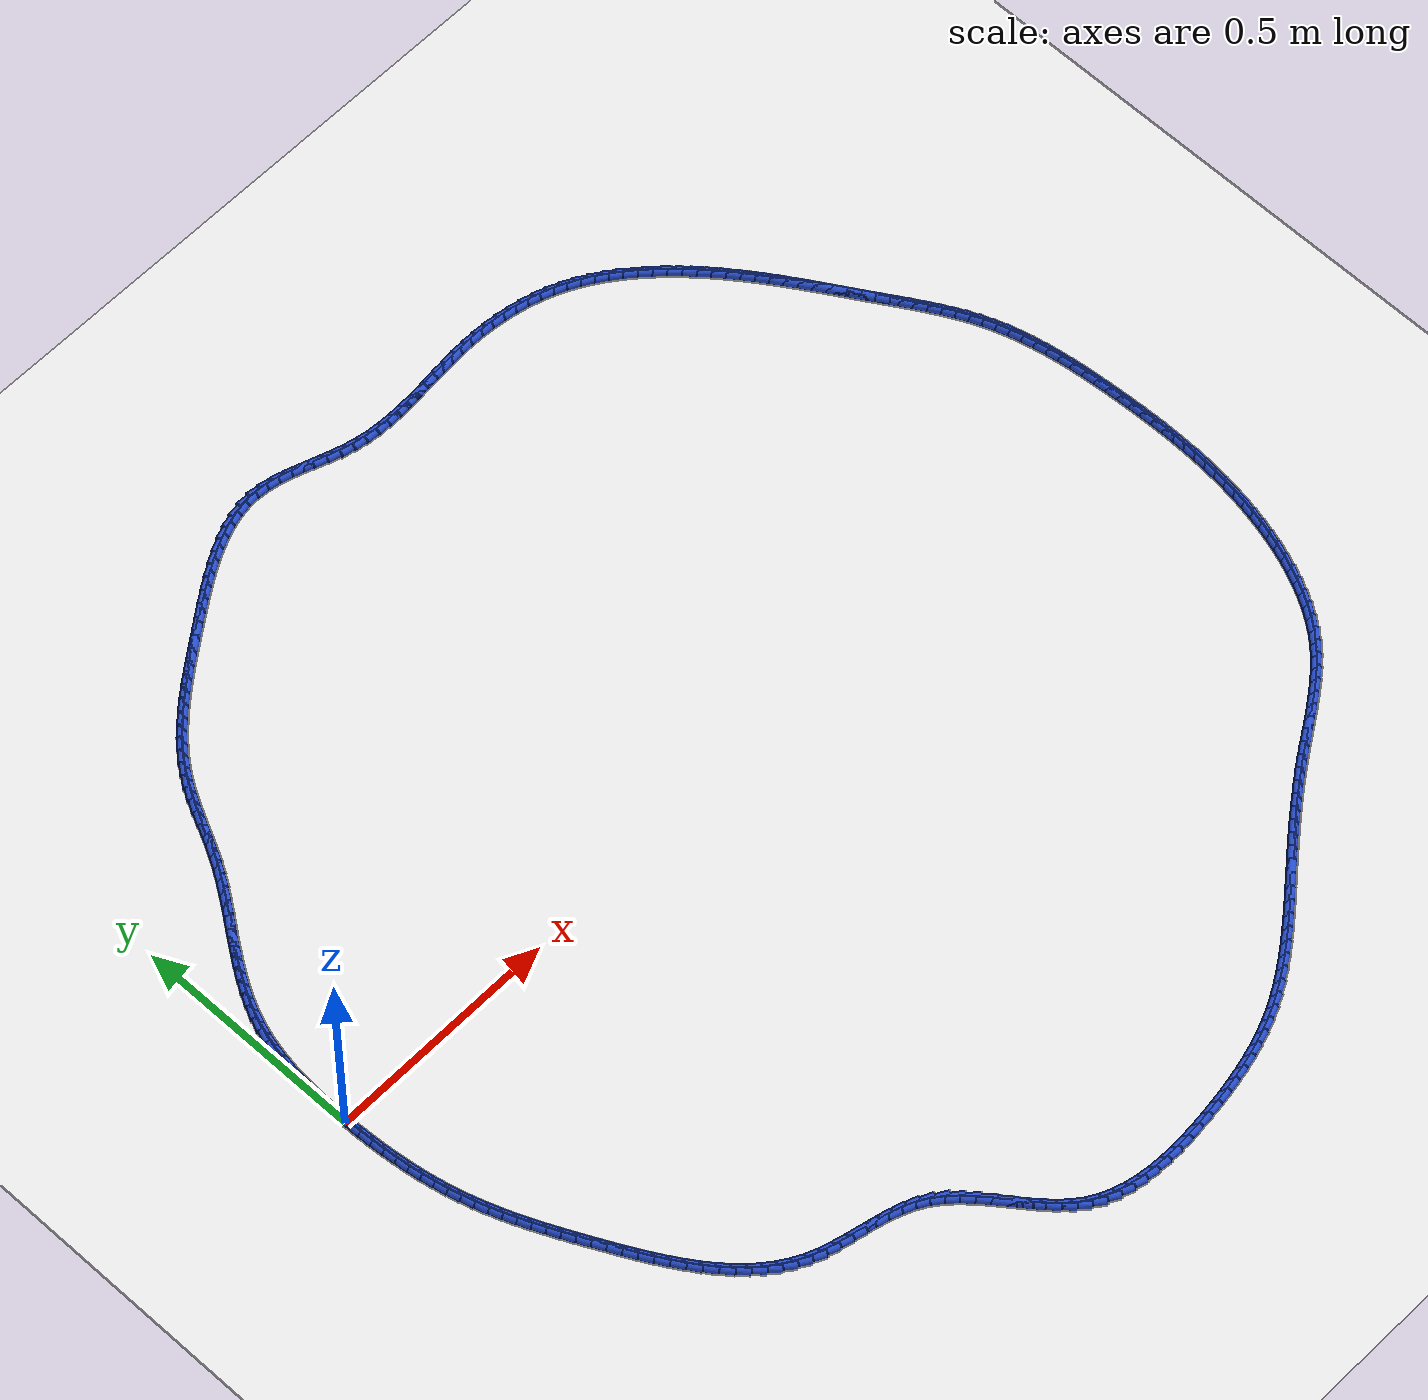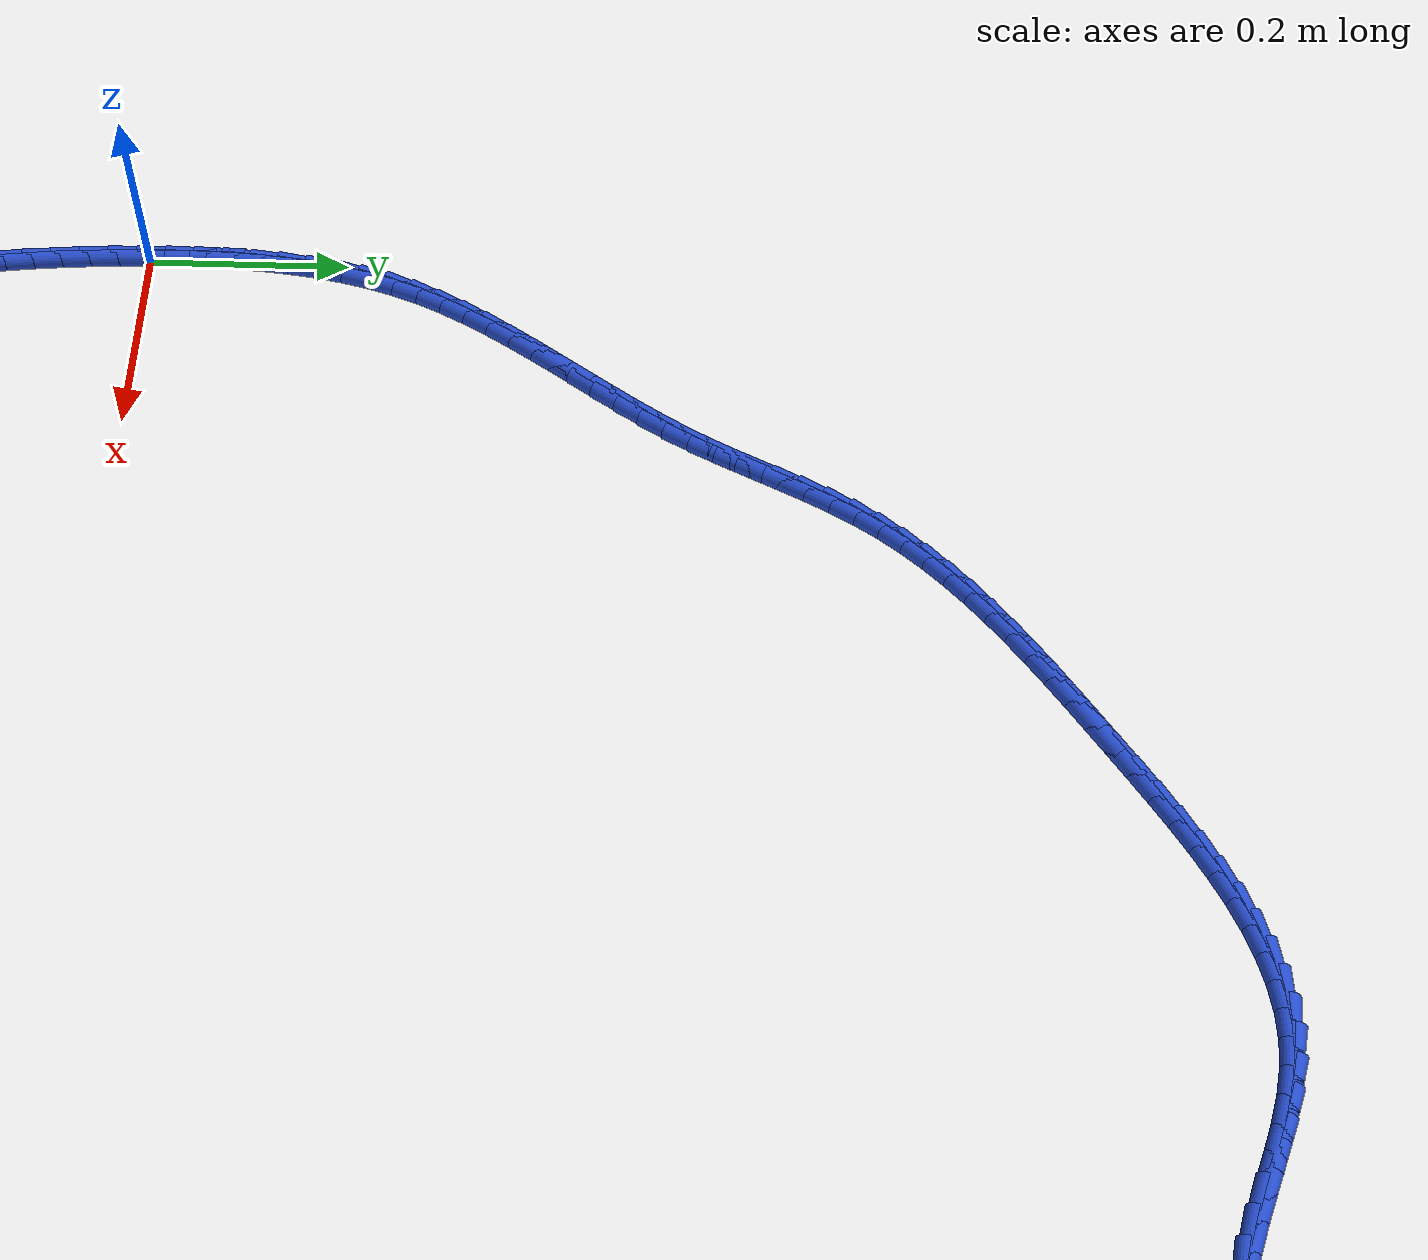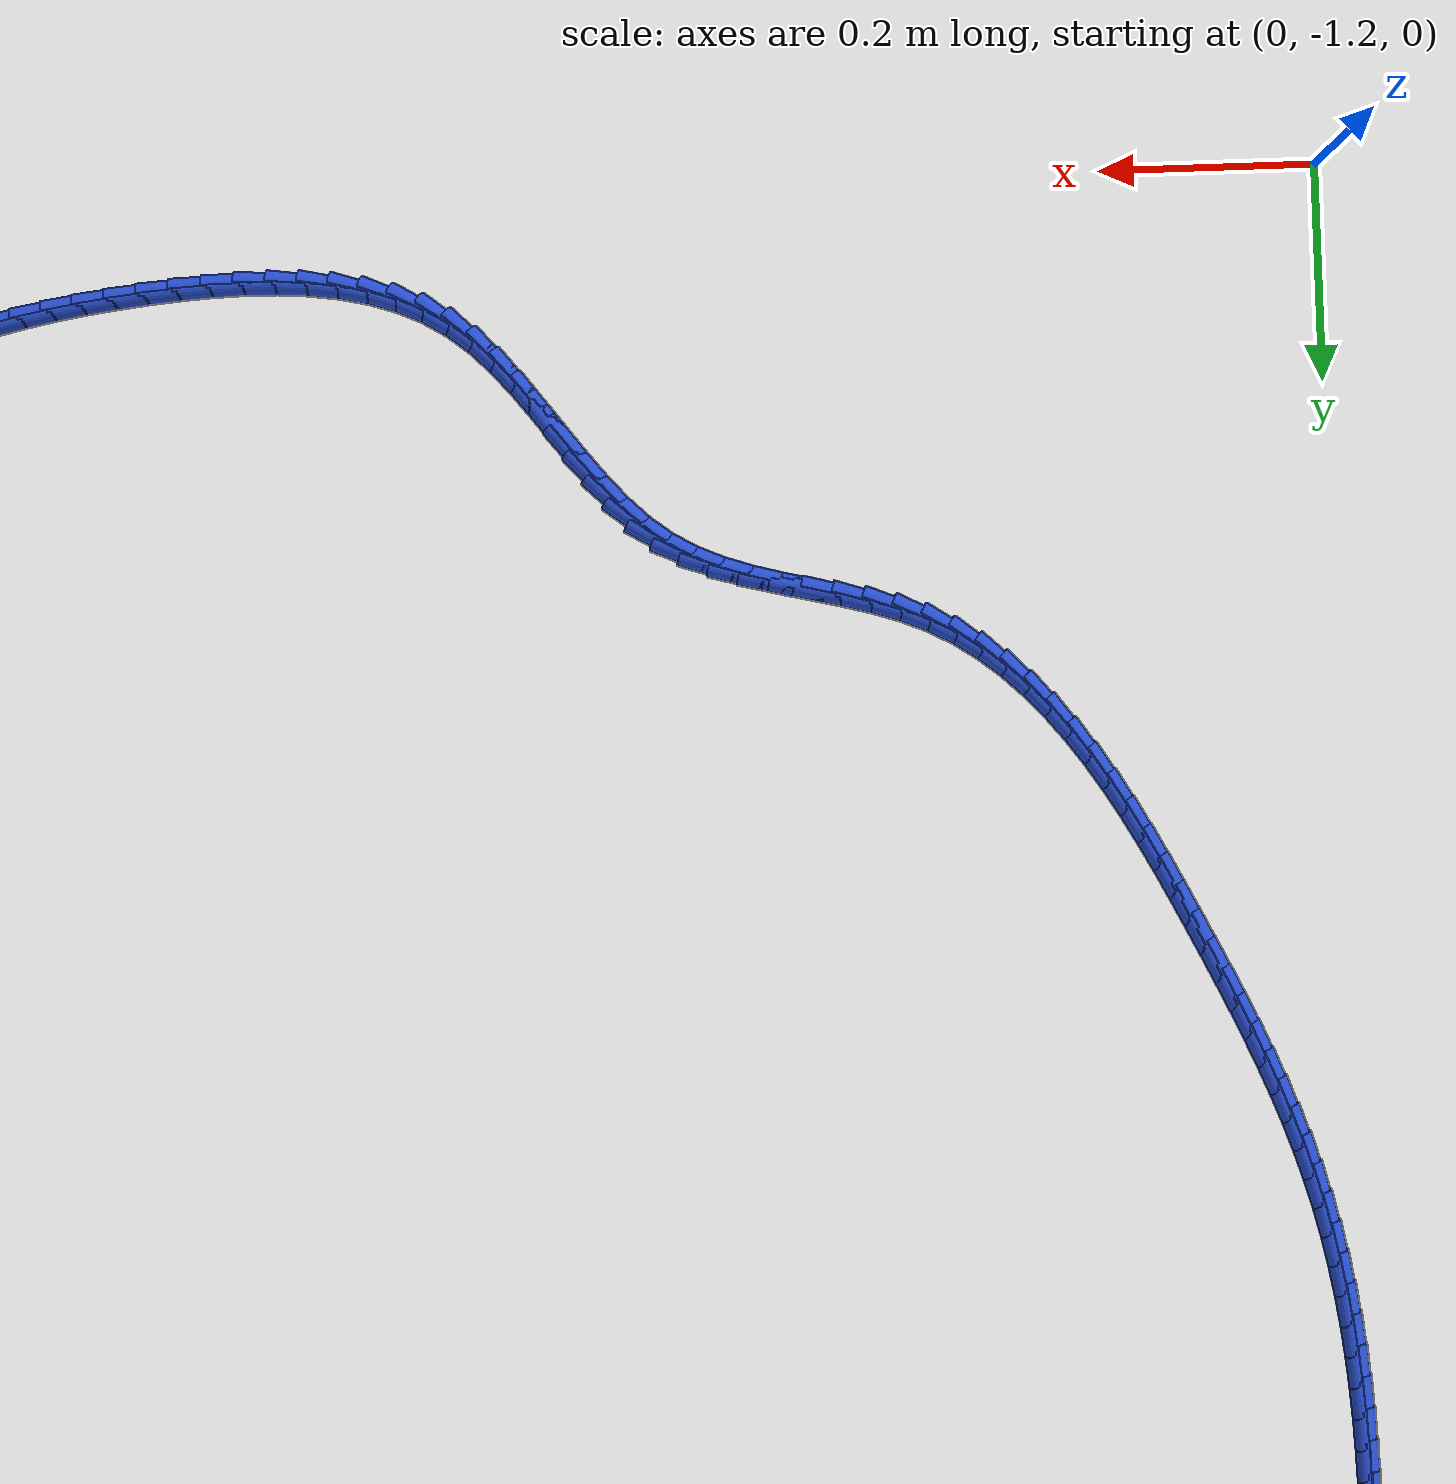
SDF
<sdf version="1.6">
 <world name="default">
  <light name="sun" type="directional">
   <pose>0 0 10 0 -0 0</pose>
   <diffuse>0.8 0.8 0.8 1</diffuse>
   <specular>0.2 0.2 0.2 1</specular>
   <attenuation>
    <range>1000</range>
    <constant>0.9</constant>
    <linear>0.01</linear>
    <quadratic>0.001</quadratic>
   </attenuation>
   <direction>-0.5 0.1 -0.9</direction>
  </light>
  <model name="ground_plane">
   <static>1</static>
   <link name="link">
    <collision name="collision">
     <geometry><plane><normal>0 0 1</normal><size>100 100</size></plane></geometry>
     <surface><friction><ode><mu>100</mu><mu2>50</mu2></ode></friction></surface>
    </collision>
    <visual name="visual">
     <cast_shadows>0</cast_shadows>
     <geometry><plane><normal>0 0 1</normal><size>100 100</size></plane></geometry>
     <material>
      <script><uri>file://media/materials/scripts/gazebo.material</uri><name>Gazebo/WhiteGlow</name></script>
     </material>
    </visual>
   </link>
  </model>
  <gravity>0 0 -9.8</gravity>
  <magnetic_field>6e-06 2.3e-05 -4.2e-05</magnetic_field>
  <atmosphere type="adiabatic"/>
  <physics name="default_physics" default="0" type="ode">
   <max_step_size>0.001</max_step_size>
   <real_time_factor>1</real_time_factor>
   <real_time_update_rate>1000</real_time_update_rate>
  </physics>
  <scene><ambient>0.4 0.4 0.4 1</ambient><background>0.7 0.7 0.7 1</background><shadows>1</shadows></scene>
  <spherical_coordinates>
   <surface_model>EARTH_WGS84</surface_model>
   <latitude_deg>0</latitude_deg>
   <longitude_deg>0</longitude_deg>
   <elevation>0</elevation>
   <heading_deg>0</heading_deg>
  </spherical_coordinates>
  <model name="line">
   <link name="link_0">
    <pose>2.2768245622195593e-17 -6.938893903907228e-17 0.01 0 1.57 -1.5595225742112602</pose>
    <collision name="collision">
     <geometry><cylinder><radius>0.01</radius><length>0.08</length></cylinder></geometry>
    </collision>
    <visual name="visual">
     <material>
      <script><name>Gazebo/Blue</name><uri>file://media/materials/scripts/gazebo.material</uri></script>
     </material>
     <geometry><cylinder><radius>0.01</radius><length>0.08</length></cylinder></geometry>
    </visual>
   </link>
   <link name="link_1">
    <pose>-0.00032222240699589856 0.02858043524278014 0.01 0 1.57 1.5596636055893285</pose>
    <collision name="collision">
     <geometry><cylinder><radius>0.01</radius><length>0.08</length></cylinder></geometry>
    </collision>
    <visual name="visual">
     <material>
      <script><name>Gazebo/Blue</name><uri>file://media/materials/scripts/gazebo.material</uri></script>
     </material>
     <geometry><cylinder><radius>0.01</radius><length>0.08</length></cylinder></geometry>
    </visual>
   </link>
   <link name="link_2">
    <pose>-3.944086268896623e-06 0.057168699142537055 0.01 0 1.57 1.5327066648585885</pose>
    <collision name="collision">
     <geometry><cylinder><radius>0.01</radius><length>0.08</length></cylinder></geometry>
    </collision>
    <visual name="visual">
     <material>
      <script><name>Gazebo/Blue</name><uri>file://media/materials/scripts/gazebo.material</uri></script>
     </material>
     <geometry><cylinder><radius>0.01</radius><length>0.08</length></cylinder></geometry>
    </visual>
   </link>
   <link name="link_3">
    <pose>0.0010824529390785905 0.08567700112342419 0.01 0 1.57 1.5009701846804488</pose>
    <collision name="collision">
     <geometry><cylinder><radius>0.01</radius><length>0.08</length></cylinder></geometry>
    </collision>
    <visual name="visual">
     <material>
      <script><name>Gazebo/Blue</name><uri>file://media/materials/scripts/gazebo.material</uri></script>
     </material>
     <geometry><cylinder><radius>0.01</radius><length>0.08</length></cylinder></geometry>
    </visual>
   </link>
   <link name="link_4">
    <pose>0.003064586645944122 0.11401755060959495 0.01 0 1.57 1.4641880685861846</pose>
    <collision name="collision">
     <geometry><cylinder><radius>0.01</radius><length>0.08</length></cylinder></geometry>
    </collision>
    <visual name="visual">
     <material>
      <script><name>Gazebo/Blue</name><uri>file://media/materials/scripts/gazebo.material</uri></script>
     </material>
     <geometry><cylinder><radius>0.01</radius><length>0.08</length></cylinder></geometry>
    </visual>
   </link>
   <link name="link_5">
    <pose>0.00607007501122526 0.14210255702520289 0.01 0 1.57 1.422075245421062</pose>
    <collision name="collision">
     <geometry><cylinder><radius>0.01</radius><length>0.08</length></cylinder></geometry>
    </collision>
    <visual name="visual">
     <material>
      <script><name>Gazebo/Blue</name><uri>file://media/materials/scripts/gazebo.material</uri></script>
     </material>
     <geometry><cylinder><radius>0.01</radius><length>0.08</length></cylinder></geometry>
    </visual>
   </link>
   <link name="link_6">
    <pose>0.010226536011819566 0.16984422979440142 0.01 0 1.57 1.3743535984373032</pose>
    <collision name="collision">
     <geometry><cylinder><radius>0.01</radius><length>0.08</length></cylinder></geometry>
    </collision>
    <visual name="visual">
     <material>
      <script><name>Gazebo/Blue</name><uri>file://media/materials/scripts/gazebo.material</uri></script>
     </material>
     <geometry><cylinder><radius>0.01</radius><length>0.08</length></cylinder></geometry>
    </visual>
   </link>
   <link name="link_7">
    <pose>0.0156615876246246 0.19715477834134418 0.01 0 1.57 1.3207881635108816</pose>
    <collision name="collision">
     <geometry><cylinder><radius>0.01</radius><length>0.08</length></cylinder></geometry>
    </collision>
    <visual name="visual">
     <material>
      <script><name>Gazebo/Blue</name><uri>file://media/materials/scripts/gazebo.material</uri></script>
     </material>
     <geometry><cylinder><radius>0.01</radius><length>0.08</length></cylinder></geometry>
    </visual>
   </link>
   <link name="link_8">
    <pose>0.022502847826537914 0.22394641209018434 0.01 0 1.57 1.2612350873705345</pose>
    <collision name="collision">
     <geometry><cylinder><radius>0.01</radius><length>0.08</length></cylinder></geometry>
    </collision>
    <visual name="visual">
     <material>
      <script><name>Gazebo/Blue</name><uri>file://media/materials/scripts/gazebo.material</uri></script>
     </material>
     <geometry><cylinder><radius>0.01</radius><length>0.08</length></cylinder></geometry>
    </visual>
   </link>
   <link name="link_9">
    <pose>0.030877934594457077 0.2501313404650757 0.01 0 1.57 1.1963981009558102</pose>
    <collision name="collision">
     <geometry><cylinder><radius>0.01</radius><length>0.08</length></cylinder></geometry>
    </collision>
    <visual name="visual">
     <material>
      <script><name>Gazebo/Blue</name><uri>file://media/materials/scripts/gazebo.material</uri></script>
     </material>
     <geometry><cylinder><radius>0.01</radius><length>0.08</length></cylinder></geometry>
    </visual>
   </link>
   <link name="link_10">
    <pose>0.04089759297079924 0.2756310843312889 0.01 0 1.57 1.1347990916974937</pose>
    <collision name="collision">
     <geometry><cylinder><radius>0.01</radius><length>0.08</length></cylinder></geometry>
    </collision>
    <visual name="visual">
     <material>
      <script><name>Gazebo/Blue</name><uri>file://media/materials/scripts/gazebo.material</uri></script>
     </material>
     <geometry><cylinder><radius>0.01</radius><length>0.08</length></cylinder></geometry>
    </visual>
   </link>
   <link name="link_11">
    <pose>0.05247334865893971 0.3004771050713818 0.01 0 1.57 1.0822572378993665</pose>
    <collision name="collision">
     <geometry><cylinder><radius>0.01</radius><length>0.08</length></cylinder></geometry>
    </collision>
    <visual name="visual">
     <material>
      <script><name>Gazebo/Blue</name><uri>file://media/materials/scripts/gazebo.material</uri></script>
     </material>
     <geometry><cylinder><radius>0.01</radius><length>0.08</length></cylinder></geometry>
    </visual>
   </link>
   <link name="link_12">
    <pose>0.06538672510684478 0.3247726066772237 0.01 0 1.57 1.0390343614038375</pose>
    <collision name="collision">
     <geometry><cylinder><radius>0.01</radius><length>0.08</length></cylinder></geometry>
    </collision>
    <visual name="visual">
     <material>
      <script><name>Gazebo/Blue</name><uri>file://media/materials/scripts/gazebo.material</uri></script>
     </material>
     <geometry><cylinder><radius>0.01</radius><length>0.08</length></cylinder></geometry>
    </visual>
   </link>
   <link name="link_13">
    <pose>0.07941701187823322 0.34862202592456326 0.01 0 1.57 1.005067085501033</pose>
    <collision name="collision">
     <geometry><cylinder><radius>0.01</radius><length>0.08</length></cylinder></geometry>
    </collision>
    <visual name="visual">
     <material>
      <script><name>Gazebo/Blue</name><uri>file://media/materials/scripts/gazebo.material</uri></script>
     </material>
     <geometry><cylinder><radius>0.01</radius><length>0.08</length></cylinder></geometry>
    </visual>
   </link>
   <link name="link_14">
    <pose>0.0943434985368238 0.37212979958914993 0.01 0 1.57 0.9801723669004929</pose>
    <collision name="collision">
     <geometry><cylinder><radius>0.01</radius><length>0.08</length></cylinder></geometry>
    </collision>
    <visual name="visual">
     <material>
      <script><name>Gazebo/Blue</name><uri>file://media/materials/scripts/gazebo.material</uri></script>
     </material>
     <geometry><cylinder><radius>0.01</radius><length>0.08</length></cylinder></geometry>
    </visual>
   </link>
   <link name="link_15">
    <pose>0.10994547464633536 0.39540036444673243 0.01 0 1.57 0.9641340377248588</pose>
    <collision name="collision">
     <geometry><cylinder><radius>0.01</radius><length>0.08</length></cylinder></geometry>
    </collision>
    <visual name="visual">
     <material>
      <script><name>Gazebo/Blue</name><uri>file://media/materials/scripts/gazebo.material</uri></script>
     </material>
     <geometry><cylinder><radius>0.01</radius><length>0.08</length></cylinder></geometry>
    </visual>
   </link>
   <link name="link_16">
    <pose>0.1260022297704866 0.4185381572730598 0.01 0 1.57 0.9567613810631997</pose>
    <collision name="collision">
     <geometry><cylinder><radius>0.01</radius><length>0.08</length></cylinder></geometry>
    </collision>
    <visual name="visual">
     <material>
      <script><name>Gazebo/Blue</name><uri>file://media/materials/scripts/gazebo.material</uri></script>
     </material>
     <geometry><cylinder><radius>0.01</radius><length>0.08</length></cylinder></geometry>
    </visual>
   </link>
   <link name="link_17">
    <pose>0.14229305347299637 0.44164761484388104 0.01 0 1.57 0.9579231480493033</pose>
    <collision name="collision">
     <geometry><cylinder><radius>0.01</radius><length>0.08</length></cylinder></geometry>
    </collision>
    <visual name="visual">
     <material>
      <script><name>Gazebo/Blue</name><uri>file://media/materials/scripts/gazebo.material</uri></script>
     </material>
     <geometry><cylinder><radius>0.01</radius><length>0.08</length></cylinder></geometry>
    </visual>
   </link>
   <link name="link_18">
    <pose>0.15859723531758346 0.4648331739349454 0.01 0 1.57 0.9675611137305057</pose>
    <collision name="collision">
     <geometry><cylinder><radius>0.01</radius><length>0.08</length></cylinder></geometry>
    </collision>
    <visual name="visual">
     <material>
      <script><name>Gazebo/Blue</name><uri>file://media/materials/scripts/gazebo.material</uri></script>
     </material>
     <geometry><cylinder><radius>0.01</radius><length>0.08</length></cylinder></geometry>
    </visual>
   </link>
   <link name="link_19">
    <pose>0.1746940648679667 0.48819927132200175 0.01 0 1.57 0.9856859068521513</pose>
    <collision name="collision">
     <geometry><cylinder><radius>0.01</radius><length>0.08</length></cylinder></geometry>
    </collision>
    <visual name="visual">
     <material>
      <script><name>Gazebo/Blue</name><uri>file://media/materials/scripts/gazebo.material</uri></script>
     </material>
     <geometry><cylinder><radius>0.01</radius><length>0.08</length></cylinder></geometry>
    </visual>
   </link>
   <link name="link_20">
    <pose>0.1903628316878648 0.5118503437807991 0.01 0 1.57 1.0123558316432582</pose>
    <collision name="collision">
     <geometry><cylinder><radius>0.01</radius><length>0.08</length></cylinder></geometry>
    </collision>
    <visual name="visual">
     <material>
      <script><name>Gazebo/Blue</name><uri>file://media/materials/scripts/gazebo.material</uri></script>
     </material>
     <geometry><cylinder><radius>0.01</radius><length>0.08</length></cylinder></geometry>
    </visual>
   </link>
   <link name="link_21">
    <pose>0.2053828253409966 0.5358908280870864 0.01 0 1.57 1.047613510016471</pose>
    <collision name="collision">
     <geometry><cylinder><radius>0.01</radius><length>0.08</length></cylinder></geometry>
    </collision>
    <visual name="visual">
     <material>
      <script><name>Gazebo/Blue</name><uri>file://media/materials/scripts/gazebo.material</uri></script>
     </material>
     <geometry><cylinder><radius>0.01</radius><length>0.08</length></cylinder></geometry>
    </visual>
   </link>
   <link name="link_22">
    <pose>0.219533916381092 0.5604247988125045 0.01 0 1.57 1.0848262253834746</pose>
    <collision name="collision">
     <geometry><cylinder><radius>0.01</radius><length>0.08</length></cylinder></geometry>
    </collision>
    <visual name="visual">
     <material>
      <script><name>Gazebo/Blue</name><uri>file://media/materials/scripts/gazebo.material</uri></script>
     </material>
     <geometry><cylinder><radius>0.01</radius><length>0.08</length></cylinder></geometry>
    </visual>
   </link>
   <link name="link_23">
    <pose>0.23275620102112984 0.5854564417338939 0.01 0 1.57 1.1083443580639825</pose>
    <collision name="collision">
     <geometry><cylinder><radius>0.01</radius><length>0.08</length></cylinder></geometry>
    </collision>
    <visual name="visual">
     <material>
      <script><name>Gazebo/Blue</name><uri>file://media/materials/scripts/gazebo.material</uri></script>
     </material>
     <geometry><cylinder><radius>0.01</radius><length>0.08</length></cylinder></geometry>
    </visual>
   </link>
   <link name="link_24">
    <pose>0.24536744147705944 0.6107544959334092 0.01 0 1.57 1.1159560403867228</pose>
    <collision name="collision">
     <geometry><cylinder><radius>0.01</radius><length>0.08</length></cylinder></geometry>
    </collision>
    <visual name="visual">
     <material>
      <script><name>Gazebo/Blue</name><uri>file://media/materials/scripts/gazebo.material</uri></script>
     </material>
     <geometry><cylinder><radius>0.01</radius><length>0.08</length></cylinder></geometry>
    </visual>
   </link>
   <link name="link_25">
    <pose>0.25773978223000543 0.6360537971911228 0.01 0 1.57 1.1075356536118606</pose>
    <collision name="collision">
     <geometry><cylinder><radius>0.01</radius><length>0.08</length></cylinder></geometry>
    </collision>
    <visual name="visual">
     <material>
      <script><name>Gazebo/Blue</name><uri>file://media/materials/scripts/gazebo.material</uri></script>
     </material>
     <geometry><cylinder><radius>0.01</radius><length>0.08</length></cylinder></geometry>
    </visual>
   </link>
   <link name="link_26">
    <pose>0.27024536776109254 0.6610891812871063 0.01 0 1.57 1.0827169568364938</pose>
    <collision name="collision">
     <geometry><cylinder><radius>0.01</radius><length>0.08</length></cylinder></geometry>
    </collision>
    <visual name="visual">
     <material>
      <script><name>Gazebo/Blue</name><uri>file://media/materials/scripts/gazebo.material</uri></script>
     </material>
     <geometry><cylinder><radius>0.01</radius><length>0.08</length></cylinder></geometry>
    </visual>
   </link>
   <link name="link_27">
    <pose>0.2832563425514456 0.6855954840014323 0.01 0 1.57 1.0409466941373826</pose>
    <collision name="collision">
     <geometry><cylinder><radius>0.01</radius><length>0.08</length></cylinder></geometry>
    </collision>
    <visual name="visual">
     <material>
      <script><name>Gazebo/Blue</name><uri>file://media/materials/scripts/gazebo.material</uri></script>
     </material>
     <geometry><cylinder><radius>0.01</radius><length>0.08</length></cylinder></geometry>
    </visual>
   </link>
   <link name="link_28">
    <pose>0.29714485108218924 0.7093075411141728 0.01 0 1.57 0.9829399287635704</pose>
    <collision name="collision">
     <geometry><cylinder><radius>0.01</radius><length>0.08</length></cylinder></geometry>
    </collision>
    <visual name="visual">
     <material>
      <script><name>Gazebo/Blue</name><uri>file://media/materials/scripts/gazebo.material</uri></script>
     </material>
     <geometry><cylinder><radius>0.01</radius><length>0.08</length></cylinder></geometry>
    </visual>
   </link>
   <link name="link_29">
    <pose>0.312256293345562 0.7319818865570717 0.01 0 1.57 0.9216318967990224</pose>
    <collision name="collision">
     <geometry><cylinder><radius>0.01</radius><length>0.08</length></cylinder></geometry>
    </collision>
    <visual name="visual">
     <material>
      <script><name>Gazebo/Blue</name><uri>file://media/materials/scripts/gazebo.material</uri></script>
     </material>
     <geometry><cylinder><radius>0.01</radius><length>0.08</length></cylinder></geometry>
    </visual>
   </link>
   <link name="link_30">
    <pose>0.32866077981837427 0.7535984002261491 0.01 0 1.57 0.8652897270511576</pose>
    <collision name="collision">
     <geometry><cylinder><radius>0.01</radius><length>0.08</length></cylinder></geometry>
    </collision>
    <visual name="visual">
     <material>
      <script><name>Gazebo/Blue</name><uri>file://media/materials/scripts/gazebo.material</uri></script>
     </material>
     <geometry><cylinder><radius>0.01</radius><length>0.08</length></cylinder></geometry>
    </visual>
   </link>
   <link name="link_31">
    <pose>0.34626638290057643 0.7742684256166454 0.01 0 1.57 0.8145436618437636</pose>
    <collision name="collision">
     <geometry><cylinder><radius>0.01</radius><length>0.08</length></cylinder></geometry>
    </collision>
    <visual name="visual">
     <material>
      <script><name>Gazebo/Blue</name><uri>file://media/materials/scripts/gazebo.material</uri></script>
     </material>
     <geometry><cylinder><radius>0.01</radius><length>0.08</length></cylinder></geometry>
    </visual>
   </link>
   <link name="link_32">
    <pose>0.3649790948919068 0.7941049938361572 0.01 0 1.57 0.7697032536656697</pose>
    <collision name="collision">
     <geometry><cylinder><radius>0.01</radius><length>0.08</length></cylinder></geometry>
    </collision>
    <visual name="visual">
     <material>
      <script><name>Gazebo/Blue</name><uri>file://media/materials/scripts/gazebo.material</uri></script>
     </material>
     <geometry><cylinder><radius>0.01</radius><length>0.08</length></cylinder></geometry>
    </visual>
   </link>
   <link name="link_33">
    <pose>0.38470490809210356 0.8132211359922803 0.01 0 1.57 0.730893830745445</pose>
    <collision name="collision">
     <geometry><cylinder><radius>0.01</radius><length>0.08</length></cylinder></geometry>
    </collision>
    <visual name="visual">
     <material>
      <script><name>Gazebo/Blue</name><uri>file://media/materials/scripts/gazebo.material</uri></script>
     </material>
     <geometry><cylinder><radius>0.01</radius><length>0.08</length></cylinder></geometry>
    </visual>
   </link>
   <link name="link_34">
    <pose>0.4053498148009052 0.8317298831926113 0.01 0 1.57 0.6981021962151122</pose>
    <collision name="collision">
     <geometry><cylinder><radius>0.01</radius><length>0.08</length></cylinder></geometry>
    </collision>
    <visual name="visual">
     <material>
      <script><name>Gazebo/Blue</name><uri>file://media/materials/scripts/gazebo.material</uri></script>
     </material>
     <geometry><cylinder><radius>0.01</radius><length>0.08</length></cylinder></geometry>
    </visual>
   </link>
   <link name="link_35">
    <pose>0.4268198073180501 0.8497442665447463 0.01 0 1.57 0.6712208617541685</pose>
    <collision name="collision">
     <geometry><cylinder><radius>0.01</radius><length>0.08</length></cylinder></geometry>
    </collision>
    <visual name="visual">
     <material>
      <script><name>Gazebo/Blue</name><uri>file://media/materials/scripts/gazebo.material</uri></script>
     </material>
     <geometry><cylinder><radius>0.01</radius><length>0.08</length></cylinder></geometry>
    </visual>
   </link>
   <link name="link_36">
    <pose>0.4490208779432763 0.8673773171562814 0.01 0 1.57 0.6500858432749537</pose>
    <collision name="collision">
     <geometry><cylinder><radius>0.01</radius><length>0.08</length></cylinder></geometry>
    </collision>
    <visual name="visual">
     <material>
      <script><name>Gazebo/Blue</name><uri>file://media/materials/scripts/gazebo.material</uri></script>
     </material>
     <geometry><cylinder><radius>0.01</radius><length>0.08</length></cylinder></geometry>
    </visual>
   </link>
   <link name="link_37">
    <pose>0.47185901897632243 0.8847420661348131 0.01 0 1.57 0.6345060488060582</pose>
    <collision name="collision">
     <geometry><cylinder><radius>0.01</radius><length>0.08</length></cylinder></geometry>
    </collision>
    <visual name="visual">
     <material>
      <script><name>Gazebo/Blue</name><uri>file://media/materials/scripts/gazebo.material</uri></script>
     </material>
     <geometry><cylinder><radius>0.01</radius><length>0.08</length></cylinder></geometry>
    </visual>
   </link>
   <link name="link_38">
    <pose>0.49524022271692675 0.9019515445879376 0.01 0 1.57 0.6242842456097483</pose>
    <collision name="collision">
     <geometry><cylinder><radius>0.01</radius><length>0.08</length></cylinder></geometry>
    </collision>
    <visual name="visual">
     <material>
      <script><name>Gazebo/Blue</name><uri>file://media/materials/scripts/gazebo.material</uri></script>
     </material>
     <geometry><cylinder><radius>0.01</radius><length>0.08</length></cylinder></geometry>
    </visual>
   </link>
   <link name="link_39">
    <pose>0.5190704814648276 0.9191187836232511 0.01 0 1.57 0.6192305894937531</pose>
    <collision name="collision">
     <geometry><cylinder><radius>0.01</radius><length>0.08</length></cylinder></geometry>
    </collision>
    <visual name="visual">
     <material>
      <script><name>Gazebo/Blue</name><uri>file://media/materials/scripts/gazebo.material</uri></script>
     </material>
     <geometry><cylinder><radius>0.01</radius><length>0.08</length></cylinder></geometry>
    </visual>
   </link>
   <link name="link_40">
    <pose>0.5432557875197632 0.9363568143483496 0.01 0 1.57 0.6175171602868582</pose>
    <collision name="collision">
     <geometry><cylinder><radius>0.01</radius><length>0.08</length></cylinder></geometry>
    </collision>
    <visual name="visual">
     <material>
      <script><name>Gazebo/Blue</name><uri>file://media/materials/scripts/gazebo.material</uri></script>
     </material>
     <geometry><cylinder><radius>0.01</radius><length>0.08</length></cylinder></geometry>
    </visual>
   </link>
   <link name="link_41">
    <pose>0.5677122469877177 0.9537249939026862 0.01 0 1.57 0.6101948304587183</pose>
    <collision name="collision">
     <geometry><cylinder><radius>0.01</radius><length>0.08</length></cylinder></geometry>
    </collision>
    <visual name="visual">
     <material>
      <script><name>Gazebo/Blue</name><uri>file://media/materials/scripts/gazebo.material</uri></script>
     </material>
     <geometry><cylinder><radius>0.01</radius><length>0.08</length></cylinder></geometry>
    </visual>
   </link>
   <link name="link_42">
    <pose>0.5924103393375251 0.9709941199976754 0.01 0 1.57 0.5942359306977779</pose>
    <collision name="collision">
     <geometry><cylinder><radius>0.01</radius><length>0.08</length></cylinder></geometry>
    </collision>
    <visual name="visual">
     <material>
      <script><name>Gazebo/Blue</name><uri>file://media/materials/scripts/gazebo.material</uri></script>
     </material>
     <geometry><cylinder><radius>0.01</radius><length>0.08</length></cylinder></geometry>
    </visual>
   </link>
   <link name="link_43">
    <pose>0.6173387372197593 0.9878384391321205 0.01 0 1.57 0.5692951589650832</pose>
    <collision name="collision">
     <geometry><cylinder><radius>0.01</radius><length>0.08</length></cylinder></geometry>
    </collision>
    <visual name="visual">
     <material>
      <script><name>Gazebo/Blue</name><uri>file://media/materials/scripts/gazebo.material</uri></script>
     </material>
     <geometry><cylinder><radius>0.01</radius><length>0.08</length></cylinder></geometry>
    </visual>
   </link>
   <link name="link_44">
    <pose>0.6424861262633675 1.0039321289285994 0.01 0 1.57 0.5347219308818583</pose>
    <collision name="collision">
     <geometry><cylinder><radius>0.01</radius><length>0.08</length></cylinder></geometry>
    </collision>
    <visual name="visual">
     <material>
      <script><name>Gazebo/Blue</name><uri>file://media/materials/scripts/gazebo.material</uri></script>
     </material>
     <geometry><cylinder><radius>0.01</radius><length>0.08</length></cylinder></geometry>
    </visual>
   </link>
   <link name="link_45">
    <pose>0.6678411920972974 1.0189493670096905 0.01 0 1.57 0.48957746124027746</pose>
    <collision name="collision">
     <geometry><cylinder><radius>0.01</radius><length>0.08</length></cylinder></geometry>
    </collision>
    <visual name="visual">
     <material>
      <script><name>Gazebo/Blue</name><uri>file://media/materials/scripts/gazebo.material</uri></script>
     </material>
     <geometry><cylinder><radius>0.01</radius><length>0.08</length></cylinder></geometry>
    </visual>
   </link>
   <link name="link_46">
    <pose>0.6933926203504956 1.032564330997971 0.01 0 1.57 0.43267981591451365</pose>
    <collision name="collision">
     <geometry><cylinder><radius>0.01</radius><length>0.08</length></cylinder></geometry>
    </collision>
    <visual name="visual">
     <material>
      <script><name>Gazebo/Blue</name><uri>file://media/materials/scripts/gazebo.material</uri></script>
     </material>
     <geometry><cylinder><radius>0.01</radius><length>0.08</length></cylinder></geometry>
    </visual>
   </link>
   <link name="link_47">
    <pose>0.7191290966519098 1.0444511985160199 0.01 0 1.57 0.3627108363635189</pose>
    <collision name="collision">
     <geometry><cylinder><radius>0.01</radius><length>0.08</length></cylinder></geometry>
    </collision>
    <visual name="visual">
     <material>
      <script><name>Gazebo/Blue</name><uri>file://media/materials/scripts/gazebo.material</uri></script>
     </material>
     <geometry><cylinder><radius>0.01</radius><length>0.08</length></cylinder></geometry>
    </visual>
   </link>
   <link name="link_48">
    <pose>0.7450393066304872 1.0542841471864146 0.01 0 1.57 0.2784374072638288</pose>
    <collision name="collision">
     <geometry><cylinder><radius>0.01</radius><length>0.08</length></cylinder></geometry>
    </collision>
    <visual name="visual">
     <material>
      <script><name>Gazebo/Blue</name><uri>file://media/materials/scripts/gazebo.material</uri></script>
     </material>
     <geometry><cylinder><radius>0.01</radius><length>0.08</length></cylinder></geometry>
    </visual>
   </link>
   <link name="link_49">
    <pose>0.7711119359151745 1.0617373546317332 0.01 0 1.57 0.17910377213596543</pose>
    <collision name="collision">
     <geometry><cylinder><radius>0.01</radius><length>0.08</length></cylinder></geometry>
    </collision>
    <visual name="visual">
     <material>
      <script><name>Gazebo/Blue</name><uri>file://media/materials/scripts/gazebo.material</uri></script>
     </material>
     <geometry><cylinder><radius>0.01</radius><length>0.08</length></cylinder></geometry>
    </visual>
   </link>
   <link name="link_50">
    <pose>0.79733567013492 1.0664849984745546 0.01 0 1.57 0.0650079812459088</pose>
    <collision name="collision">
     <geometry><cylinder><radius>0.01</radius><length>0.08</length></cylinder></geometry>
    </collision>
    <visual name="visual">
     <material>
      <script><name>Gazebo/Blue</name><uri>file://media/materials/scripts/gazebo.material</uri></script>
     </material>
     <geometry><cylinder><radius>0.01</radius><length>0.08</length></cylinder></geometry>
    </visual>
   </link>
   <link name="link_51">
    <pose>0.8236991949186696 1.0682012563374554 0.01 0 1.57 -0.061111362508018456</pose>
    <collision name="collision">
     <geometry><cylinder><radius>0.01</radius><length>0.08</length></cylinder></geometry>
    </collision>
    <visual name="visual">
     <material>
      <script><name>Gazebo/Blue</name><uri>file://media/materials/scripts/gazebo.material</uri></script>
     </material>
     <geometry><cylinder><radius>0.01</radius><length>0.08</length></cylinder></geometry>
    </visual>
   </link>
   <link name="link_52">
    <pose>0.8501913987057045 1.0665802632460781 0.01 0 1.57 -0.17630340702647132</pose>
    <collision name="collision">
     <geometry><cylinder><radius>0.01</radius><length>0.08</length></cylinder></geometry>
    </collision>
    <visual name="visual">
     <material>
      <script><name>Gazebo/Blue</name><uri>file://media/materials/scripts/gazebo.material</uri></script>
     </material>
     <geometry><cylinder><radius>0.01</radius><length>0.08</length></cylinder></geometry>
    </visual>
   </link>
   <link name="link_53">
    <pose>0.8768064801748737 1.0618387044830315 0.01 0 1.57 -0.25902541707026466</pose>
    <collision name="collision">
     <geometry><cylinder><radius>0.01</radius><length>0.08</length></cylinder></geometry>
    </collision>
    <visual name="visual">
     <material>
      <script><name>Gazebo/Blue</name><uri>file://media/materials/scripts/gazebo.material</uri></script>
     </material>
     <geometry><cylinder><radius>0.01</radius><length>0.08</length></cylinder></geometry>
    </visual>
   </link>
   <link name="link_54">
    <pose>0.9035443337864383 1.0547537545518695 0.01 0 1.57 -0.31065342686190267</pose>
    <collision name="collision">
     <geometry><cylinder><radius>0.01</radius><length>0.08</length></cylinder></geometry>
    </collision>
    <visual name="visual">
     <material>
      <script><name>Gazebo/Blue</name><uri>file://media/materials/scripts/gazebo.material</uri></script>
     </material>
     <geometry><cylinder><radius>0.01</radius><length>0.08</length></cylinder></geometry>
    </visual>
   </link>
   <link name="link_55">
    <pose>0.9304051340381215 1.0461301448387874 0.01 0 1.57 -0.3338051287900811</pose>
    <collision name="collision">
     <geometry><cylinder><radius>0.01</radius><length>0.08</length></cylinder></geometry>
    </collision>
    <visual name="visual">
     <material>
      <script><name>Gazebo/Blue</name><uri>file://media/materials/scripts/gazebo.material</uri></script>
     </material>
     <geometry><cylinder><radius>0.01</radius><length>0.08</length></cylinder></geometry>
    </visual>
   </link>
   <link name="link_56">
    <pose>0.9573890554276485 1.0367726067299807 0.01 0 1.57 -0.3300607233329601</pose>
    <collision name="collision">
     <geometry><cylinder><radius>0.01</radius><length>0.08</length></cylinder></geometry>
    </collision>
    <visual name="visual">
     <material>
      <script><name>Gazebo/Blue</name><uri>file://media/materials/scripts/gazebo.material</uri></script>
     </material>
     <geometry><cylinder><radius>0.01</radius><length>0.08</length></cylinder></geometry>
    </visual>
   </link>
   <link name="link_57">
    <pose>0.9844962724527424 1.027485871611645 0.01 0 1.57 -0.299589780737403</pose>
    <collision name="collision">
     <geometry><cylinder><radius>0.01</radius><length>0.08</length></cylinder></geometry>
    </collision>
    <visual name="visual">
     <material>
      <script><name>Gazebo/Blue</name><uri>file://media/materials/scripts/gazebo.material</uri></script>
     </material>
     <geometry><cylinder><radius>0.01</radius><length>0.08</length></cylinder></geometry>
    </visual>
   </link>
   <link name="link_58">
    <pose>1.011726959611128 1.0190746708699765 0.01 0 1.57 -0.24128502930555937</pose>
    <collision name="collision">
     <geometry><cylinder><radius>0.01</radius><length>0.08</length></cylinder></geometry>
    </collision>
    <visual name="visual">
     <material>
      <script><name>Gazebo/Blue</name><uri>file://media/materials/scripts/gazebo.material</uri></script>
     </material>
     <geometry><cylinder><radius>0.01</radius><length>0.08</length></cylinder></geometry>
    </visual>
   </link>
   <link name="link_59">
    <pose>1.0390812889827286 1.0123433416572625 0.01 0 1.57 -0.16289647095071633</pose>
    <collision name="collision">
     <geometry><cylinder><radius>0.01</radius><length>0.08</length></cylinder></geometry>
    </collision>
    <visual name="visual">
     <material>
      <script><name>Gazebo/Blue</name><uri>file://media/materials/scripts/gazebo.material</uri></script>
     </material>
     <geometry><cylinder><radius>0.01</radius><length>0.08</length></cylinder></geometry>
    </visual>
   </link>
   <link name="link_60">
    <pose>1.0665577846280159 1.007827503664897 0.01 0 1.57 -0.09038923001171945</pose>
    <collision name="collision">
     <geometry><cylinder><radius>0.01</radius><length>0.08</length></cylinder></geometry>
    </collision>
    <visual name="visual">
     <material>
      <script><name>Gazebo/Blue</name><uri>file://media/materials/scripts/gazebo.material</uri></script>
     </material>
     <geometry><cylinder><radius>0.01</radius><length>0.08</length></cylinder></geometry>
    </visual>
   </link>
   <link name="link_61">
    <pose>1.09415045575763 1.0053266087067578 0.01 0 1.57 -0.029283162239596233</pose>
    <collision name="collision">
     <geometry><cylinder><radius>0.01</radius><length>0.08</length></cylinder></geometry>
    </collision>
    <visual name="visual">
     <material>
      <script><name>Gazebo/Blue</name><uri>file://media/materials/scripts/gazebo.material</uri></script>
     </material>
     <geometry><cylinder><radius>0.01</radius><length>0.08</length></cylinder></geometry>
    </visual>
   </link>
   <link name="link_62">
    <pose>1.1218525453573984 1.004515171972734 0.01 0 1.57 0.019869408805196217</pose>
    <collision name="collision">
     <geometry><cylinder><radius>0.01</radius><length>0.08</length></cylinder></geometry>
    </collision>
    <visual name="visual">
     <material>
      <script><name>Gazebo/Blue</name><uri>file://media/materials/scripts/gazebo.material</uri></script>
     </material>
     <geometry><cylinder><radius>0.01</radius><length>0.08</length></cylinder></geometry>
    </visual>
   </link>
   <link name="link_63">
    <pose>1.1496572964131482 1.005067708652714 0.01 0 1.57 0.05696296524713587</pose>
    <collision name="collision">
     <geometry><cylinder><radius>0.01</radius><length>0.08</length></cylinder></geometry>
    </collision>
    <visual name="visual">
     <material>
      <script><name>Gazebo/Blue</name><uri>file://media/materials/scripts/gazebo.material</uri></script>
     </material>
     <geometry><cylinder><radius>0.01</radius><length>0.08</length></cylinder></geometry>
    </visual>
   </link>
   <link name="link_64">
    <pose>1.177557951910704 1.006658733936586 0.01 0 1.57 0.08213155598495231</pose>
    <collision name="collision">
     <geometry><cylinder><radius>0.01</radius><length>0.08</length></cylinder></geometry>
    </collision>
    <visual name="visual">
     <material>
      <script><name>Gazebo/Blue</name><uri>file://media/materials/scripts/gazebo.material</uri></script>
     </material>
     <geometry><cylinder><radius>0.01</radius><length>0.08</length></cylinder></geometry>
    </visual>
   </link>
   <link name="link_65">
    <pose>1.2055477548358933 1.0089627630142388 0.01 0 1.57 0.09558731416901978</pose>
    <collision name="collision">
     <geometry><cylinder><radius>0.01</radius><length>0.08</length></cylinder></geometry>
    </collision>
    <visual name="visual">
     <material>
      <script><name>Gazebo/Blue</name><uri>file://media/materials/scripts/gazebo.material</uri></script>
     </material>
     <geometry><cylinder><radius>0.01</radius><length>0.08</length></cylinder></geometry>
    </visual>
   </link>
   <link name="link_66">
    <pose>1.233619948174543 1.0116543110755607 0.01 0 1.57 0.09751546858803624</pose>
    <collision name="collision">
     <geometry><cylinder><radius>0.01</radius><length>0.08</length></cylinder></geometry>
    </collision>
    <visual name="visual">
     <material>
      <script><name>Gazebo/Blue</name><uri>file://media/materials/scripts/gazebo.material</uri></script>
     </material>
     <geometry><cylinder><radius>0.01</radius><length>0.08</length></cylinder></geometry>
    </visual>
   </link>
   <link name="link_67">
    <pose>1.2617677749124787 1.0144078933104406 0.01 0 1.57 0.08802223120758317</pose>
    <collision name="collision">
     <geometry><cylinder><radius>0.01</radius><length>0.08</length></cylinder></geometry>
    </collision>
    <visual name="visual">
     <material>
      <script><name>Gazebo/Blue</name><uri>file://media/materials/scripts/gazebo.material</uri></script>
     </material>
     <geometry><cylinder><radius>0.01</radius><length>0.08</length></cylinder></geometry>
    </visual>
   </link>
   <link name="link_68">
    <pose>1.2899844780355267 1.0168980249087665 0.01 0 1.57 0.0671293677111708</pose>
    <collision name="collision">
     <geometry><cylinder><radius>0.01</radius><length>0.08</length></cylinder></geometry>
    </collision>
    <visual name="visual">
     <material>
      <script><name>Gazebo/Blue</name><uri>file://media/materials/scripts/gazebo.material</uri></script>
     </material>
     <geometry><cylinder><radius>0.01</radius><length>0.08</length></cylinder></geometry>
    </visual>
   </link>
   <link name="link_69">
    <pose>1.3182633005295146 1.0187992210604273 0.01 0 1.57 0.034812268123149415</pose>
    <collision name="collision">
     <geometry><cylinder><radius>0.01</radius><length>0.08</length></cylinder></geometry>
    </collision>
    <visual name="visual">
     <material>
      <script><name>Gazebo/Blue</name><uri>file://media/materials/scripts/gazebo.material</uri></script>
     </material>
     <geometry><cylinder><radius>0.01</radius><length>0.08</length></cylinder></geometry>
    </visual>
   </link>
   <link name="link_70">
    <pose>1.346597485380268 1.0197859969553116 0.01 0 1.57 -0.0075205285078051454</pose>
    <collision name="collision">
     <geometry><cylinder><radius>0.01</radius><length>0.08</length></cylinder></geometry>
    </collision>
    <visual name="visual">
     <material>
      <script><name>Gazebo/Blue</name><uri>file://media/materials/scripts/gazebo.material</uri></script>
     </material>
     <geometry><cylinder><radius>0.01</radius><length>0.08</length></cylinder></geometry>
    </visual>
   </link>
   <link name="link_71">
    <pose>1.3749644129799756 1.019572658645583 0.01 0 1.57 -0.05391742898823277</pose>
    <collision name="collision">
     <geometry><cylinder><radius>0.01</radius><length>0.08</length></cylinder></geometry>
    </collision>
    <visual name="visual">
     <material>
      <script><name>Gazebo/Blue</name><uri>file://media/materials/scripts/gazebo.material</uri></script>
     </material>
     <geometry><cylinder><radius>0.01</radius><length>0.08</length></cylinder></geometry>
    </visual>
   </link>
   <link name="link_72">
    <pose>1.4032731628967807 1.0180448428462787 0.01 0 1.57 -0.1030600554830914</pose>
    <collision name="collision">
     <geometry><cylinder><radius>0.01</radius><length>0.08</length></cylinder></geometry>
    </collision>
    <visual name="visual">
     <material>
      <script><name>Gazebo/Blue</name><uri>file://media/materials/scripts/gazebo.material</uri></script>
     </material>
     <geometry><cylinder><radius>0.01</radius><length>0.08</length></cylinder></geometry>
    </visual>
   </link>
   <link name="link_73">
    <pose>1.431414435596673 1.0151342897243172 0.01 0 1.57 -0.1552672594832462</pose>
    <collision name="collision">
     <geometry><cylinder><radius>0.01</radius><length>0.08</length></cylinder></geometry>
    </collision>
    <visual name="visual">
     <material>
      <script><name>Gazebo/Blue</name><uri>file://media/materials/scripts/gazebo.material</uri></script>
     </material>
     <geometry><cylinder><radius>0.01</radius><length>0.08</length></cylinder></geometry>
    </visual>
   </link>
   <link name="link_74">
    <pose>1.4592789312928902 1.0107727400806397 0.01 0 1.57 -0.21083489125790836</pose>
    <collision name="collision">
     <geometry><cylinder><radius>0.01</radius><length>0.08</length></cylinder></geometry>
    </collision>
    <visual name="visual">
     <material>
      <script><name>Gazebo/Blue</name><uri>file://media/materials/scripts/gazebo.material</uri></script>
     </material>
     <geometry><cylinder><radius>0.01</radius><length>0.08</length></cylinder></geometry>
    </visual>
   </link>
   <link name="link_75">
    <pose>1.4867573501986697 1.0048919347161878 0.01 0 1.57 -0.27001871910243197</pose>
    <collision name="collision">
     <geometry><cylinder><radius>0.01</radius><length>0.08</length></cylinder></geometry>
    </collision>
    <visual name="visual">
     <material>
      <script><name>Gazebo/Blue</name><uri>file://media/materials/scripts/gazebo.material</uri></script>
     </material>
     <geometry><cylinder><radius>0.01</radius><length>0.08</length></cylinder></geometry>
    </visual>
   </link>
   <link name="link_76">
    <pose>1.513740392527249 0.9974236144319025 0.01 0 1.57 -0.3330114237377714</pose>
    <collision name="collision">
     <geometry><cylinder><radius>0.01</radius><length>0.08</length></cylinder></geometry>
    </collision>
    <visual name="visual">
     <material>
      <script><name>Gazebo/Blue</name><uri>file://media/materials/scripts/gazebo.material</uri></script>
     </material>
     <geometry><cylinder><radius>0.01</radius><length>0.08</length></cylinder></geometry>
    </visual>
   </link>
   <link name="link_77">
    <pose>1.5401187584918665 0.9882995200287258 0.01 0 1.57 -0.399752509041242</pose>
    <collision name="collision">
     <geometry><cylinder><radius>0.01</radius><length>0.08</length></cylinder></geometry>
    </collision>
    <visual name="visual">
     <material>
      <script><name>Gazebo/Blue</name><uri>file://media/materials/scripts/gazebo.material</uri></script>
     </material>
     <geometry><cylinder><radius>0.01</radius><length>0.08</length></cylinder></geometry>
    </visual>
   </link>
   <link name="link_78">
    <pose>1.5657853531439214 0.9774553448193805 0.01 0 1.57 -0.46627773351622187</pose>
    <collision name="collision">
     <geometry><cylinder><radius>0.01</radius><length>0.08</length></cylinder></geometry>
    </collision>
    <visual name="visual">
     <material>
      <script><name>Gazebo/Blue</name><uri>file://media/materials/scripts/gazebo.material</uri></script>
     </material>
     <geometry><cylinder><radius>0.01</radius><length>0.08</length></cylinder></geometry>
    </visual>
   </link>
   <link name="link_79">
    <pose>1.5906866106589983 0.9649227413111007 0.01 0 1.57 -0.5283933904988294</pose>
    <collision name="collision">
     <geometry><cylinder><radius>0.01</radius><length>0.08</length></cylinder></geometry>
    </collision>
    <visual name="visual">
     <material>
      <script><name>Gazebo/Blue</name><uri>file://media/materials/scripts/gazebo.material</uri></script>
     </material>
     <geometry><cylinder><radius>0.01</radius><length>0.08</length></cylinder></geometry>
    </visual>
   </link>
   <link name="link_80">
    <pose>1.6148241082456831 0.9508322143855952 0.01 0 1.57 -0.5858728921140296</pose>
    <collision name="collision">
     <geometry><cylinder><radius>0.01</radius><length>0.08</length></cylinder></geometry>
    </collision>
    <visual name="visual">
     <material>
      <script><name>Gazebo/Blue</name><uri>file://media/materials/scripts/gazebo.material</uri></script>
     </material>
     <geometry><cylinder><radius>0.01</radius><length>0.08</length></cylinder></geometry>
    </visual>
   </link>
   <link name="link_81">
    <pose>1.6382019508217687 0.9353188002324027 0.01 0 1.57 -0.6388038422222837</pose>
    <collision name="collision">
     <geometry><cylinder><radius>0.01</radius><length>0.08</length></cylinder></geometry>
    </collision>
    <visual name="visual">
     <material>
      <script><name>Gazebo/Blue</name><uri>file://media/materials/scripts/gazebo.material</uri></script>
     </material>
     <geometry><cylinder><radius>0.01</radius><length>0.08</length></cylinder></geometry>
    </visual>
   </link>
   <link name="link_82">
    <pose>1.6608242433050477 0.9185175350410641 0.01 0 1.57 -0.6873637962840522</pose>
    <collision name="collision">
     <geometry><cylinder><radius>0.01</radius><length>0.08</length></cylinder></geometry>
    </collision>
    <visual name="visual">
     <material>
      <script><name>Gazebo/Blue</name><uri>file://media/materials/scripts/gazebo.material</uri></script>
     </material>
     <geometry><cylinder><radius>0.01</radius><length>0.08</length></cylinder></geometry>
    </visual>
   </link>
   <link name="link_83">
    <pose>1.6826950906133145 0.9005634550011201 0.01 0 1.57 -0.731786318917979</pose>
    <collision name="collision">
     <geometry><cylinder><radius>0.01</radius><length>0.08</length></cylinder></geometry>
    </collision>
    <visual name="visual">
     <material>
      <script><name>Gazebo/Blue</name><uri>file://media/materials/scripts/gazebo.material</uri></script>
     </material>
     <geometry><cylinder><radius>0.01</radius><length>0.08</length></cylinder></geometry>
    </visual>
   </link>
   <link name="link_84">
    <pose>1.703818597664363 0.8815915963021103 0.01 0 1.57 -0.7723338587616769</pose>
    <collision name="collision">
     <geometry><cylinder><radius>0.01</radius><length>0.08</length></cylinder></geometry>
    </collision>
    <visual name="visual">
     <material>
      <script><name>Gazebo/Blue</name><uri>file://media/materials/scripts/gazebo.material</uri></script>
     </material>
     <geometry><cylinder><radius>0.01</radius><length>0.08</length></cylinder></geometry>
    </visual>
   </link>
   <link name="link_85">
    <pose>1.7241988693759853 0.8617369951335744 0.01 0 1.57 -0.8092774155509176</pose>
    <collision name="collision">
     <geometry><cylinder><radius>0.01</radius><length>0.08</length></cylinder></geometry>
    </collision>
    <visual name="visual">
     <material>
      <script><name>Gazebo/Blue</name><uri>file://media/materials/scripts/gazebo.material</uri></script>
     </material>
     <geometry><cylinder><radius>0.01</radius><length>0.08</length></cylinder></geometry>
    </visual>
   </link>
   <link name="link_86">
    <pose>1.743840010665975 0.8411346876850534 0.01 0 1.57 -0.8428820918112516</pose>
    <collision name="collision">
     <geometry><cylinder><radius>0.01</radius><length>0.08</length></cylinder></geometry>
    </collision>
    <visual name="visual">
     <material>
      <script><name>Gazebo/Blue</name><uri>file://media/materials/scripts/gazebo.material</uri></script>
     </material>
     <geometry><cylinder><radius>0.01</radius><length>0.08</length></cylinder></geometry>
    </visual>
   </link>
   <link name="link_87">
    <pose>1.7627461264521262 0.8199197101460872 0.01 0 1.57 -0.8733997879962678</pose>
    <collision name="collision">
     <geometry><cylinder><radius>0.01</radius><length>0.08</length></cylinder></geometry>
    </collision>
    <visual name="visual">
     <material>
      <script><name>Gazebo/Blue</name><uri>file://media/materials/scripts/gazebo.material</uri></script>
     </material>
     <geometry><cylinder><radius>0.01</radius><length>0.08</length></cylinder></geometry>
    </visual>
   </link>
   <link name="link_88">
    <pose>1.780921827457331 0.7982263848692446 0.01 0 1.57 -0.9011440772615743</pose>
    <collision name="collision">
     <geometry><cylinder><radius>0.01</radius><length>0.08</length></cylinder></geometry>
    </collision>
    <visual name="visual">
     <material>
      <script><name>Gazebo/Blue</name><uri>file://media/materials/scripts/gazebo.material</uri></script>
     </material>
     <geometry><cylinder><radius>0.01</radius><length>0.08</length></cylinder></geometry>
    </visual>
   </link>
   <link name="link_89">
    <pose>1.79839886893319 0.7761507254430474 0.01 0 1.57 -0.9262599156094407</pose>
    <collision name="collision">
     <geometry><cylinder><radius>0.01</radius><length>0.08</length></cylinder></geometry>
    </collision>
    <visual name="visual">
     <material>
      <script><name>Gazebo/Blue</name><uri>file://media/materials/scripts/gazebo.material</uri></script>
     </material>
     <geometry><cylinder><radius>0.01</radius><length>0.08</length></cylinder></geometry>
    </visual>
   </link>
   <link name="link_90">
    <pose>1.8152493346173466 0.7537318303232237 0.01 0 1.57 -0.94864955188879</pose>
    <collision name="collision">
     <geometry><cylinder><radius>0.01</radius><length>0.08</length></cylinder></geometry>
    </collision>
    <visual name="visual">
     <material>
      <script><name>Gazebo/Blue</name><uri>file://media/materials/scripts/gazebo.material</uri></script>
     </material>
     <geometry><cylinder><radius>0.01</radius><length>0.08</length></cylinder></geometry>
    </visual>
   </link>
   <link name="link_91">
    <pose>1.8315485810788399 0.7310041790558486 0.01 0 1.57 -0.9682268597767398</pose>
    <collision name="collision">
     <geometry><cylinder><radius>0.01</radius><length>0.08</length></cylinder></geometry>
    </collision>
    <visual name="visual">
     <material>
      <script><name>Gazebo/Blue</name><uri>file://media/materials/scripts/gazebo.material</uri></script>
     </material>
     <geometry><cylinder><radius>0.01</radius><length>0.08</length></cylinder></geometry>
    </visual>
   </link>
   <link name="link_92">
    <pose>1.847371964886707 0.7080022511869972 0.01 0 1.57 -0.984929691876685</pose>
    <collision name="collision">
     <geometry><cylinder><radius>0.01</radius><length>0.08</length></cylinder></geometry>
    </collision>
    <visual name="visual">
     <material>
      <script><name>Gazebo/Blue</name><uri>file://media/materials/scripts/gazebo.material</uri></script>
     </material>
     <geometry><cylinder><radius>0.01</radius><length>0.08</length></cylinder></geometry>
    </visual>
   </link>
   <link name="link_93">
    <pose>1.862794842609987 0.6847605262627453 0.01 0 1.57 -0.9987159368080589</pose>
    <collision name="collision">
     <geometry><cylinder><radius>0.01</radius><length>0.08</length></cylinder></geometry>
    </collision>
    <visual name="visual">
     <material>
      <script><name>Gazebo/Blue</name><uri>file://media/materials/scripts/gazebo.material</uri></script>
     </material>
     <geometry><cylinder><radius>0.01</radius><length>0.08</length></cylinder></geometry>
    </visual>
   </link>
   <link name="link_94">
    <pose>1.8778925708177172 0.6613134838291685 0.01 0 1.57 -1.0095597619470347</pose>
    <collision name="collision">
     <geometry><cylinder><radius>0.01</radius><length>0.08</length></cylinder></geometry>
    </collision>
    <visual name="visual">
     <material>
      <script><name>Gazebo/Blue</name><uri>file://media/materials/scripts/gazebo.material</uri></script>
     </material>
     <geometry><cylinder><radius>0.01</radius><length>0.08</length></cylinder></geometry>
    </visual>
   </link>
   <link name="link_95">
    <pose>1.8927405060789362 0.6376956034323422 0.01 0 1.57 -1.0174482753391745</pose>
    <collision name="collision">
     <geometry><cylinder><radius>0.01</radius><length>0.08</length></cylinder></geometry>
    </collision>
    <visual name="visual">
     <material>
      <script><name>Gazebo/Blue</name><uri>file://media/materials/scripts/gazebo.material</uri></script>
     </material>
     <geometry><cylinder><radius>0.01</radius><length>0.08</length></cylinder></geometry>
    </visual>
   </link>
   <link name="link_96">
    <pose>1.9074140049626818 0.6139413646183414 0.01 0 1.57 -1.0223787666242508</pose>
    <collision name="collision">
     <geometry><cylinder><radius>0.01</radius><length>0.08</length></cylinder></geometry>
    </collision>
    <visual name="visual">
     <material>
      <script><name>Gazebo/Blue</name><uri>file://media/materials/scripts/gazebo.material</uri></script>
     </material>
     <geometry><cylinder><radius>0.01</radius><length>0.08</length></cylinder></geometry>
    </visual>
   </link>
   <link name="link_97">
    <pose>1.9219884240379932 0.5900852469332424 0.01 0 1.57 -1.0243566253499228</pose>
    <collision name="collision">
     <geometry><cylinder><radius>0.01</radius><length>0.08</length></cylinder></geometry>
    </collision>
    <visual name="visual">
     <material>
      <script><name>Gazebo/Blue</name><uri>file://media/materials/scripts/gazebo.material</uri></script>
     </material>
     <geometry><cylinder><radius>0.01</radius><length>0.08</length></cylinder></geometry>
    </visual>
   </link>
   <link name="link_98">
    <pose>1.9365391198739073 0.5661617299231201 0.01 0 1.57 -1.0233939872345128</pose>
    <collision name="collision">
     <geometry><cylinder><radius>0.01</radius><length>0.08</length></cylinder></geometry>
    </collision>
    <visual name="visual">
     <material>
      <script><name>Gazebo/Blue</name><uri>file://media/materials/scripts/gazebo.material</uri></script>
     </material>
     <geometry><cylinder><radius>0.01</radius><length>0.08</length></cylinder></geometry>
    </visual>
   </link>
   <link name="link_99">
    <pose>1.9511414490394627 0.5422052931340501 0.01 0 1.57 -1.0201546986422705</pose>
    <collision name="collision">
     <geometry><cylinder><radius>0.01</radius><length>0.08</length></cylinder></geometry>
    </collision>
    <visual name="visual">
     <material>
      <script><name>Gazebo/Blue</name><uri>file://media/materials/scripts/gazebo.material</uri></script>
     </material>
     <geometry><cylinder><radius>0.01</radius><length>0.08</length></cylinder></geometry>
    </visual>
   </link>
   <link name="link_100">
    <pose>1.9658534430049892 0.5182439372726724 0.01 0 1.57 -1.0205119480425129</pose>
    <collision name="collision">
     <geometry><cylinder><radius>0.01</radius><length>0.08</length></cylinder></geometry>
    </collision>
    <visual name="visual">
     <material>
      <script><name>Gazebo/Blue</name><uri>file://media/materials/scripts/gazebo.material</uri></script>
     </material>
     <geometry><cylinder><radius>0.01</radius><length>0.08</length></cylinder></geometry>
    </visual>
   </link>
   <link name="link_101">
    <pose>1.9805756270959236 0.4942467625429519 0.01 0 1.57 -1.027584034571957</pose>
    <collision name="collision">
     <geometry><cylinder><radius>0.01</radius><length>0.08</length></cylinder></geometry>
    </collision>
    <visual name="visual">
     <material>
      <script><name>Gazebo/Blue</name><uri>file://media/materials/scripts/gazebo.material</uri></script>
     </material>
     <geometry><cylinder><radius>0.01</radius><length>0.08</length></cylinder></geometry>
    </visual>
   </link>
   <link name="link_102">
    <pose>1.9951244911435757 0.47015144349971455 0.01 0 1.57 -1.0414350865432203</pose>
    <collision name="collision">
     <geometry><cylinder><radius>0.01</radius><length>0.08</length></cylinder></geometry>
    </collision>
    <visual name="visual">
     <material>
      <script><name>Gazebo/Blue</name><uri>file://media/materials/scripts/gazebo.material</uri></script>
     </material>
     <geometry><cylinder><radius>0.01</radius><length>0.08</length></cylinder></geometry>
    </visual>
   </link>
   <link name="link_103">
    <pose>2.0093157378839623 0.4458953603581048 0.01 0 1.57 -1.0621499600653668</pose>
    <collision name="collision">
     <geometry><cylinder><radius>0.01</radius><length>0.08</length></cylinder></geometry>
    </collision>
    <visual name="visual">
     <material>
      <script><name>Gazebo/Blue</name><uri>file://media/materials/scripts/gazebo.material</uri></script>
     </material>
     <geometry><cylinder><radius>0.01</radius><length>0.08</length></cylinder></geometry>
    </visual>
   </link>
   <link name="link_104">
    <pose>2.0229650700531003 0.42141589333326696 0.01 0 1.57 -1.0898454058800702</pose>
    <collision name="collision">
     <geometry><cylinder><radius>0.01</radius><length>0.08</length></cylinder></geometry>
    </collision>
    <visual name="visual">
     <material>
      <script><name>Gazebo/Blue</name><uri>file://media/materials/scripts/gazebo.material</uri></script>
     </material>
     <geometry><cylinder><radius>0.01</radius><length>0.08</length></cylinder></geometry>
    </visual>
   </link>
   <link name="link_105">
    <pose>2.035888190387005 0.39665042264034633 0.01 0 1.57 -1.1246414334945056</pose>
    <collision name="collision">
     <geometry><cylinder><radius>0.01</radius><length>0.08</length></cylinder></geometry>
    </collision>
    <visual name="visual">
     <material>
      <script><name>Gazebo/Blue</name><uri>file://media/materials/scripts/gazebo.material</uri></script>
     </material>
     <geometry><cylinder><radius>0.01</radius><length>0.08</length></cylinder></geometry>
    </visual>
   </link>
   <link name="link_106">
    <pose>2.047900801621694 0.3715363284944872 0.01 0 1.57 -1.166620510187034</pose>
    <collision name="collision">
     <geometry><cylinder><radius>0.01</radius><length>0.08</length></cylinder></geometry>
    </collision>
    <visual name="visual">
     <material>
      <script><name>Gazebo/Blue</name><uri>file://media/materials/scripts/gazebo.material</uri></script>
     </material>
     <geometry><cylinder><radius>0.01</radius><length>0.08</length></cylinder></geometry>
    </visual>
   </link>
   <link name="link_107">
    <pose>2.058818606493184 0.34601099111083455 0.01 0 1.57 -1.215040180983089</pose>
    <collision name="collision">
     <geometry><cylinder><radius>0.01</radius><length>0.08</length></cylinder></geometry>
    </collision>
    <visual name="visual">
     <material>
      <script><name>Gazebo/Blue</name><uri>file://media/materials/scripts/gazebo.material</uri></script>
     </material>
     <geometry><cylinder><radius>0.01</radius><length>0.08</length></cylinder></geometry>
    </visual>
   </link>
   <link name="link_108">
    <pose>2.068476248232542 0.3200192250488251 0.01 0 1.57 -1.2630410361164</pose>
    <collision name="collision">
     <geometry><cylinder><radius>0.01</radius><length>0.08</length></cylinder></geometry>
    </collision>
    <visual name="visual">
     <material>
      <script><name>Gazebo/Blue</name><uri>file://media/materials/scripts/gazebo.material</uri></script>
     </material>
     <geometry><cylinder><radius>0.01</radius><length>0.08</length></cylinder></geometry>
    </visual>
   </link>
   <link name="link_109">
    <pose>2.0768819789267847 0.2935739881769246 0.01 0 1.57 -1.3068747012392117</pose>
    <collision name="collision">
     <geometry><cylinder><radius>0.01</radius><length>0.08</length></cylinder></geometry>
    </collision>
    <visual name="visual">
     <material>
      <script><name>Gazebo/Blue</name><uri>file://media/materials/scripts/gazebo.material</uri></script>
     </material>
     <geometry><cylinder><radius>0.01</radius><length>0.08</length></cylinder></geometry>
    </visual>
   </link>
   <link name="link_110">
    <pose>2.0841372933922653 0.2667248371193751 0.01 0 1.57 -1.3464547459250875</pose>
    <collision name="collision">
     <geometry><cylinder><radius>0.01</radius><length>0.08</length></cylinder></geometry>
    </collision>
    <visual name="visual">
     <material>
      <script><name>Gazebo/Blue</name><uri>file://media/materials/scripts/gazebo.material</uri></script>
     </material>
     <geometry><cylinder><radius>0.01</radius><length>0.08</length></cylinder></geometry>
    </visual>
   </link>
   <link name="link_111">
    <pose>2.09034457975218 0.23952167913278763 0.01 0 1.57 -1.381797230077032</pose>
    <collision name="collision">
     <geometry><cylinder><radius>0.01</radius><length>0.08</length></cylinder></geometry>
    </collision>
    <visual name="visual">
     <material>
      <script><name>Gazebo/Blue</name><uri>file://media/materials/scripts/gazebo.material</uri></script>
     </material>
     <geometry><cylinder><radius>0.01</radius><length>0.08</length></cylinder></geometry>
    </visual>
   </link>
   <link name="link_112">
    <pose>2.0956062261297266 0.212014421473773 0.01 0 1.57 -1.412964345646461</pose>
    <collision name="collision">
     <geometry><cylinder><radius>0.01</radius><length>0.08</length></cylinder></geometry>
    </collision>
    <visual name="visual">
     <material>
      <script><name>Gazebo/Blue</name><uri>file://media/materials/scripts/gazebo.material</uri></script>
     </material>
     <geometry><cylinder><radius>0.01</radius><length>0.08</length></cylinder></geometry>
    </visual>
   </link>
   <link name="link_113">
    <pose>2.100024620648103 0.1842529713989432 0.01 0 1.57 -1.440045248858083</pose>
    <collision name="collision">
     <geometry><cylinder><radius>0.01</radius><length>0.08</length></cylinder></geometry>
    </collision>
    <visual name="visual">
     <material>
      <script><name>Gazebo/Blue</name><uri>file://media/materials/scripts/gazebo.material</uri></script>
     </material>
     <geometry><cylinder><radius>0.01</radius><length>0.08</length></cylinder></geometry>
    </visual>
   </link>
   <link name="link_114">
    <pose>2.1037021514305074 0.15628723616490897 0.01 0 1.57 -1.4631400976650224</pose>
    <collision name="collision">
     <geometry><cylinder><radius>0.01</radius><length>0.08</length></cylinder></geometry>
    </collision>
    <visual name="visual">
     <material>
      <script><name>Gazebo/Blue</name><uri>file://media/materials/scripts/gazebo.material</uri></script>
     </material>
     <geometry><cylinder><radius>0.01</radius><length>0.08</length></cylinder></geometry>
    </visual>
   </link>
   <link name="link_115">
    <pose>2.106741206600137 0.12816712302828115 0.01 0 1.57 -1.482347292651821</pose>
    <collision name="collision">
     <geometry><cylinder><radius>0.01</radius><length>0.08</length></cylinder></geometry>
    </collision>
    <visual name="visual">
     <material>
      <script><name>Gazebo/Blue</name><uri>file://media/materials/scripts/gazebo.material</uri></script>
     </material>
     <geometry><cylinder><radius>0.01</radius><length>0.08</length></cylinder></geometry>
    </visual>
   </link>
   <link name="link_116">
    <pose>2.109244174280188 0.09994253924567165 0.01 0 1.57 -1.4977535658598222</pose>
    <collision name="collision">
     <geometry><cylinder><radius>0.01</radius><length>0.08</length></cylinder></geometry>
    </collision>
    <visual name="visual">
     <material>
      <script><name>Gazebo/Blue</name><uri>file://media/materials/scripts/gazebo.material</uri></script>
     </material>
     <geometry><cylinder><radius>0.01</radius><length>0.08</length></cylinder></geometry>
    </visual>
   </link>
   <link name="link_117">
    <pose>2.1113134425938602 0.0716633920736913 0.01 0 1.57 -1.5097330350895222</pose>
    <collision name="collision">
     <geometry><cylinder><radius>0.01</radius><length>0.08</length></cylinder></geometry>
    </collision>
    <visual name="visual">
     <material>
      <script><name>Gazebo/Blue</name><uri>file://media/materials/scripts/gazebo.material</uri></script>
     </material>
     <geometry><cylinder><radius>0.01</radius><length>0.08</length></cylinder></geometry>
    </visual>
   </link>
   <link name="link_118">
    <pose>2.1130428424657066 0.04337716964380964 0.01 0 1.57 -1.521429081852297</pose>
    <collision name="collision">
     <geometry><cylinder><radius>0.01</radius><length>0.08</length></cylinder></geometry>
    </collision>
    <visual name="visual">
     <material>
      <script><name>Gazebo/Blue</name><uri>file://media/materials/scripts/gazebo.material</uri></script>
     </material>
     <geometry><cylinder><radius>0.01</radius><length>0.08</length></cylinder></geometry>
    </visual>
   </link>
   <link name="link_119">
    <pose>2.1144396037603133 0.015106877916379673 0.01 0 1.57 -1.5346632644618854</pose>
    <collision name="collision">
     <geometry><cylinder><radius>0.01</radius><length>0.08</length></cylinder></geometry>
    </collision>
    <visual name="visual">
     <material>
      <script><name>Gazebo/Blue</name><uri>file://media/materials/scripts/gazebo.material</uri></script>
     </material>
     <geometry><cylinder><radius>0.01</radius><length>0.08</length></cylinder></geometry>
    </visual>
   </link>
   <link name="link_120">
    <pose>2.115460647366896 -0.013138699525478184 0.01 0 1.57 -1.5494745631688358</pose>
    <collision name="collision">
     <geometry><cylinder><radius>0.01</radius><length>0.08</length></cylinder></geometry>
    </collision>
    <visual name="visual">
     <material>
      <script><name>Gazebo/Blue</name><uri>file://media/materials/scripts/gazebo.material</uri></script>
     </material>
     <geometry><cylinder><radius>0.01</radius><length>0.08</length></cylinder></geometry>
    </visual>
   </link>
   <link name="link_121">
    <pose>2.1160622735724615 -0.041350954543257976 0.01 0 1.57 -1.5658795223888713</pose>
    <collision name="collision">
     <geometry><cylinder><radius>0.01</radius><length>0.08</length></cylinder></geometry>
    </collision>
    <visual name="visual">
     <material>
      <script><name>Gazebo/Blue</name><uri>file://media/materials/scripts/gazebo.material</uri></script>
     </material>
     <geometry><cylinder><radius>0.01</radius><length>0.08</length></cylinder></geometry>
    </visual>
   </link>
   <link name="link_122">
    <pose>2.1162007826640146 -0.06952127899845345 0.01 0 1.57 1.5576992612823624</pose>
    <collision name="collision">
     <geometry><cylinder><radius>0.01</radius><length>0.08</length></cylinder></geometry>
    </collision>
    <visual name="visual">
     <material>
      <script><name>Gazebo/Blue</name><uri>file://media/materials/scripts/gazebo.material</uri></script>
     </material>
     <geometry><cylinder><radius>0.01</radius><length>0.08</length></cylinder></geometry>
    </visual>
   </link>
   <link name="link_123">
    <pose>2.1158324749285615 -0.09764106475255827 0.01 0 1.57 1.538063782604587</pose>
    <collision name="collision">
     <geometry><cylinder><radius>0.01</radius><length>0.08</length></cylinder></geometry>
    </collision>
    <visual name="visual">
     <material>
      <script><name>Gazebo/Blue</name><uri>file://media/materials/scripts/gazebo.material</uri></script>
     </material>
     <geometry><cylinder><radius>0.01</radius><length>0.08</length></cylinder></geometry>
    </visual>
   </link>
   <link name="link_124">
    <pose>2.1149136506531097 -0.1257017036670662 0.01 0 1.57 1.5167979727776215</pose>
    <collision name="collision">
     <geometry><cylinder><radius>0.01</radius><length>0.08</length></cylinder></geometry>
    </collision>
    <visual name="visual">
     <material>
      <script><name>Gazebo/Blue</name><uri>file://media/materials/scripts/gazebo.material</uri></script>
     </material>
     <geometry><cylinder><radius>0.01</radius><length>0.08</length></cylinder></geometry>
    </visual>
   </link>
   <link name="link_125">
    <pose>2.113400610124664 -0.15369458760347166 0.01 0 1.57 1.493898667466999</pose>
    <collision name="collision">
     <geometry><cylinder><radius>0.01</radius><length>0.08</length></cylinder></geometry>
    </collision>
    <visual name="visual">
     <material>
      <script><name>Gazebo/Blue</name><uri>file://media/materials/scripts/gazebo.material</uri></script>
     </material>
     <geometry><cylinder><radius>0.01</radius><length>0.08</length></cylinder></geometry>
    </visual>
   </link>
   <link name="link_126">
    <pose>2.111249653630231 -0.1816111084232669 0.01 0 1.57 1.4693699824782473</pose>
    <collision name="collision">
     <geometry><cylinder><radius>0.01</radius><length>0.08</length></cylinder></geometry>
    </collision>
    <visual name="visual">
     <material>
      <script><name>Gazebo/Blue</name><uri>file://media/materials/scripts/gazebo.material</uri></script>
     </material>
     <geometry><cylinder><radius>0.01</radius><length>0.08</length></cylinder></geometry>
    </visual>
   </link>
   <link name="link_127">
    <pose>2.108417081456816 -0.20944265798794626 0.01 0 1.57 1.4432251406906664</pose>
    <collision name="collision">
     <geometry><cylinder><radius>0.01</radius><length>0.08</length></cylinder></geometry>
    </collision>
    <visual name="visual">
     <material>
      <script><name>Gazebo/Blue</name><uri>file://media/materials/scripts/gazebo.material</uri></script>
     </material>
     <geometry><cylinder><radius>0.01</radius><length>0.08</length></cylinder></geometry>
    </visual>
   </link>
   <link name="link_128">
    <pose>2.1048591938914267 -0.2371806281590036 0.01 0 1.57 1.415488350202008</pose>
    <collision name="collision">
     <geometry><cylinder><radius>0.01</radius><length>0.08</length></cylinder></geometry>
    </collision>
    <visual name="visual">
     <material>
      <script><name>Gazebo/Blue</name><uri>file://media/materials/scripts/gazebo.material</uri></script>
     </material>
     <geometry><cylinder><radius>0.01</radius><length>0.08</length></cylinder></geometry>
    </visual>
   </link>
   <link name="link_129">
    <pose>2.1005322912210675 -0.2648164107979325 0.01 0 1.57 1.3861966591097032</pose>
    <collision name="collision">
     <geometry><cylinder><radius>0.01</radius><length>0.08</length></cylinder></geometry>
    </collision>
    <visual name="visual">
     <material>
      <script><name>Gazebo/Blue</name><uri>file://media/materials/scripts/gazebo.material</uri></script>
     </material>
     <geometry><cylinder><radius>0.01</radius><length>0.08</length></cylinder></geometry>
    </visual>
   </link>
   <link name="link_130">
    <pose>2.0953926737327455 -0.2923413977662268 0.01 0 1.57 1.3554016909524944</pose>
    <collision name="collision">
     <geometry><cylinder><radius>0.01</radius><length>0.08</length></cylinder></geometry>
    </collision>
    <visual name="visual">
     <material>
      <script><name>Gazebo/Blue</name><uri>file://media/materials/scripts/gazebo.material</uri></script>
     </material>
     <geometry><cylinder><radius>0.01</radius><length>0.08</length></cylinder></geometry>
    </visual>
   </link>
   <link name="link_131">
    <pose>2.0893966417134666 -0.3197469809253801 0.01 0 1.57 1.3231711455250543</pose>
    <collision name="collision">
     <geometry><cylinder><radius>0.01</radius><length>0.08</length></cylinder></geometry>
    </collision>
    <visual name="visual">
     <material>
      <script><name>Gazebo/Blue</name><uri>file://media/materials/scripts/gazebo.material</uri></script>
     </material>
     <geometry><cylinder><radius>0.01</radius><length>0.08</length></cylinder></geometry>
    </visual>
   </link>
   <link name="link_132">
    <pose>2.0825004954502364 -0.3470245521368869 0.01 0 1.57 1.2895899348451574</pose>
    <collision name="collision">
     <geometry><cylinder><radius>0.01</radius><length>0.08</length></cylinder></geometry>
    </collision>
    <visual name="visual">
     <material>
      <script><name>Gazebo/Blue</name><uri>file://media/materials/scripts/gazebo.material</uri></script>
     </material>
     <geometry><cylinder><radius>0.01</radius><length>0.08</length></cylinder></geometry>
    </visual>
   </link>
   <link name="link_133">
    <pose>2.074660535226977 -0.3741655031680019 0.01 0 1.57 1.2544783435317768</pose>
    <collision name="collision">
     <geometry><cylinder><radius>0.01</radius><length>0.08</length></cylinder></geometry>
    </collision>
    <visual name="visual">
     <material>
      <script><name>Gazebo/Blue</name><uri>file://media/materials/scripts/gazebo.material</uri></script>
     </material>
     <geometry><cylinder><radius>0.01</radius><length>0.08</length></cylinder></geometry>
    </visual>
   </link>
   <link name="link_134">
    <pose>2.06583229392095 -0.4011377783418549 0.01 0 1.57 1.216696519978977</pose>
    <collision name="collision">
     <geometry><cylinder><radius>0.01</radius><length>0.08</length></cylinder></geometry>
    </collision>
    <visual name="visual">
     <material>
      <script><name>Gazebo/Blue</name><uri>file://media/materials/scripts/gazebo.material</uri></script>
     </material>
     <geometry><cylinder><radius>0.01</radius><length>0.08</length></cylinder></geometry>
    </visual>
   </link>
   <link name="link_135">
    <pose>2.055968379969773 -0.42781996826768565 0.01 0 1.57 1.1756670518471042</pose>
    <collision name="collision">
     <geometry><cylinder><radius>0.01</radius><length>0.08</length></cylinder></geometry>
    </collision>
    <visual name="visual">
     <material>
      <script><name>Gazebo/Blue</name><uri>file://media/materials/scripts/gazebo.material</uri></script>
     </material>
     <geometry><cylinder><radius>0.01</radius><length>0.08</length></cylinder></geometry>
    </visual>
   </link>
   <link name="link_136">
    <pose>2.045020705296711 -0.45406938216347736 0.01 0 1.57 1.1310281730745018</pose>
    <collision name="collision">
     <geometry><cylinder><radius>0.01</radius><length>0.08</length></cylinder></geometry>
    </collision>
    <visual name="visual">
     <material>
      <script><name>Gazebo/Blue</name><uri>file://media/materials/scripts/gazebo.material</uri></script>
     </material>
     <geometry><cylinder><radius>0.01</radius><length>0.08</length></cylinder></geometry>
    </visual>
   </link>
   <link name="link_137">
    <pose>2.0329411818250263 -0.47974332924721297 0.01 0 1.57 1.0824093386403797</pose>
    <collision name="collision">
     <geometry><cylinder><radius>0.01</radius><length>0.08</length></cylinder></geometry>
    </collision>
    <visual name="visual">
     <material>
      <script><name>Gazebo/Blue</name><uri>file://media/materials/scripts/gazebo.material</uri></script>
     </material>
     <geometry><cylinder><radius>0.01</radius><length>0.08</length></cylinder></geometry>
    </visual>
   </link>
   <link name="link_138">
    <pose>2.019681721477983 -0.5046991187368757 0.01 0 1.57 1.0294459630793122</pose>
    <collision name="collision">
     <geometry><cylinder><radius>0.01</radius><length>0.08</length></cylinder></geometry>
    </collision>
    <visual name="visual">
     <material>
      <script><name>Gazebo/Blue</name><uri>file://media/materials/scripts/gazebo.material</uri></script>
     </material>
     <geometry><cylinder><radius>0.01</radius><length>0.08</length></cylinder></geometry>
    </visual>
   </link>
   <link name="link_139">
    <pose>2.0051942361788466 -0.5287940598504488 0.01 0 1.57 0.9718023439021031</pose>
    <collision name="collision">
     <geometry><cylinder><radius>0.01</radius><length>0.08</length></cylinder></geometry>
    </collision>
    <visual name="visual">
     <material>
      <script><name>Gazebo/Blue</name><uri>file://media/materials/scripts/gazebo.material</uri></script>
     </material>
     <geometry><cylinder><radius>0.01</radius><length>0.08</length></cylinder></geometry>
    </visual>
   </link>
   <link name="link_140">
    <pose>1.989430637850879 -0.5518854618059158 0.01 0 1.57 0.9092045008138666</pose>
    <collision name="collision">
     <geometry><cylinder><radius>0.01</radius><length>0.08</length></cylinder></geometry>
    </collision>
    <visual name="visual">
     <material>
      <script><name>Gazebo/Blue</name><uri>file://media/materials/scripts/gazebo.material</uri></script>
     </material>
     <geometry><cylinder><radius>0.01</radius><length>0.08</length></cylinder></geometry>
    </visual>
   </link>
   <link name="link_141">
    <pose>1.9723428384173465 -0.5738306338212589 0.01 0 1.57 0.8415528188620068</pose>
    <collision name="collision">
     <geometry><cylinder><radius>0.01</radius><length>0.08</length></cylinder></geometry>
    </collision>
    <visual name="visual">
     <material>
      <script><name>Gazebo/Blue</name><uri>file://media/materials/scripts/gazebo.material</uri></script>
     </material>
     <geometry><cylinder><radius>0.01</radius><length>0.08</length></cylinder></geometry>
    </visual>
   </link>
   <link name="link_142">
    <pose>1.9538839090354243 -0.5944884630910923 0.01 0 1.57 0.774004521325926</pose>
    <collision name="collision">
     <geometry><cylinder><radius>0.01</radius><length>0.08</length></cylinder></geometry>
    </collision>
    <visual name="visual">
     <material>
      <script><name>Gazebo/Blue</name><uri>file://media/materials/scripts/gazebo.material</uri></script>
     </material>
     <geometry><cylinder><radius>0.01</radius><length>0.08</length></cylinder></geometry>
    </visual>
   </link>
   <link name="link_143">
    <pose>1.9340923340909006 -0.6138341033177619 0.01 0 1.57 0.7154957164285846</pose>
    <collision name="collision">
     <geometry><cylinder><radius>0.01</radius><length>0.08</length></cylinder></geometry>
    </collision>
    <visual name="visual">
     <material>
      <script><name>Gazebo/Blue</name><uri>file://media/materials/scripts/gazebo.material</uri></script>
     </material>
     <geometry><cylinder><radius>0.01</radius><length>0.08</length></cylinder></geometry>
    </visual>
   </link>
   <link name="link_144">
    <pose>1.9131490153663124 -0.6320365701337849 0.01 0 1.57 0.6670701601685041</pose>
    <collision name="collision">
     <geometry><cylinder><radius>0.01</radius><length>0.08</length></cylinder></geometry>
    </collision>
    <visual name="visual">
     <material>
      <script><name>Gazebo/Blue</name><uri>file://media/materials/scripts/gazebo.material</uri></script>
     </material>
     <geometry><cylinder><radius>0.01</radius><length>0.08</length></cylinder></geometry>
    </visual>
   </link>
   <link name="link_145">
    <pose>1.8912483574201229 -0.6492832594697555 0.01 0 1.57 0.6286720355768992</pose>
    <collision name="collision">
     <geometry><cylinder><radius>0.01</radius><length>0.08</length></cylinder></geometry>
    </collision>
    <visual name="visual">
     <material>
      <script><name>Gazebo/Blue</name><uri>file://media/materials/scripts/gazebo.material</uri></script>
     </material>
     <geometry><cylinder><radius>0.01</radius><length>0.08</length></cylinder></geometry>
    </visual>
   </link>
   <link name="link_146">
    <pose>1.8685847648107963 -0.6657615672562686 0.01 0 1.57 0.6000988588178695</pose>
    <collision name="collision">
     <geometry><cylinder><radius>0.01</radius><length>0.08</length></cylinder></geometry>
    </collision>
    <visual name="visual">
     <material>
      <script><name>Gazebo/Blue</name><uri>file://media/materials/scripts/gazebo.material</uri></script>
     </material>
     <geometry><cylinder><radius>0.01</radius><length>0.08</length></cylinder></geometry>
    </visual>
   </link>
   <link name="link_147">
    <pose>1.8453526420967963 -0.681658889423919 0.01 0 1.57 0.5811154966232107</pose>
    <collision name="collision">
     <geometry><cylinder><radius>0.01</radius><length>0.08</length></cylinder></geometry>
    </collision>
    <visual name="visual">
     <material>
      <script><name>Gazebo/Blue</name><uri>file://media/materials/scripts/gazebo.material</uri></script>
     </material>
     <geometry><cylinder><radius>0.01</radius><length>0.08</length></cylinder></geometry>
    </visual>
   </link>
   <link name="link_148">
    <pose>1.8217463938365868 -0.6971626219033004 0.01 0 1.57 0.5715325563070818</pose>
    <collision name="collision">
     <geometry><cylinder><radius>0.01</radius><length>0.08</length></cylinder></geometry>
    </collision>
    <visual name="visual">
     <material>
      <script><name>Gazebo/Blue</name><uri>file://media/materials/scripts/gazebo.material</uri></script>
     </material>
     <geometry><cylinder><radius>0.01</radius><length>0.08</length></cylinder></geometry>
    </visual>
   </link>
   <link name="link_149">
    <pose>1.7979604245886311 -0.7124601606250077 0.01 0 1.57 0.5712541330028025</pose>
    <collision name="collision">
     <geometry><cylinder><radius>0.01</radius><length>0.08</length></cylinder></geometry>
    </collision>
    <visual name="visual">
     <material>
      <script><name>Gazebo/Blue</name><uri>file://media/materials/scripts/gazebo.material</uri></script>
     </material>
     <geometry><cylinder><radius>0.01</radius><length>0.08</length></cylinder></geometry>
    </visual>
   </link>
   <link name="link_150">
    <pose>1.7741891389113935 -0.7277389015196358 0.01 0 1.57 0.5803007376888554</pose>
    <collision name="collision">
     <geometry><cylinder><radius>0.01</radius><length>0.08</length></cylinder></geometry>
    </collision>
    <visual name="visual">
     <material>
      <script><name>Gazebo/Blue</name><uri>file://media/materials/scripts/gazebo.material</uri></script>
     </material>
     <geometry><cylinder><radius>0.01</radius><length>0.08</length></cylinder></geometry>
    </visual>
   </link>
   <link name="link_151">
    <pose>1.7506269407687653 -0.7431862400159723 0.01 0 1.57 0.5968161331320111</pose>
    <collision name="collision">
     <geometry><cylinder><radius>0.01</radius><length>0.08</length></cylinder></geometry>
    </collision>
    <visual name="visual">
     <material>
      <script><name>Gazebo/Blue</name><uri>file://media/materials/scripts/gazebo.material</uri></script>
     </material>
     <geometry><cylinder><radius>0.01</radius><length>0.08</length></cylinder></geometry>
    </visual>
   </link>
   <link name="link_152">
    <pose>1.7274238494025729 -0.7589521117374592 0.01 0 1.57 0.6134725327199605</pose>
    <collision name="collision">
     <geometry><cylinder><radius>0.01</radius><length>0.08</length></cylinder></geometry>
    </collision>
    <visual name="visual">
     <material>
      <script><name>Gazebo/Blue</name><uri>file://media/materials/scripts/gazebo.material</uri></script>
     </material>
     <geometry><cylinder><radius>0.01</radius><length>0.08</length></cylinder></geometry>
    </visual>
   </link>
   <link name="link_153">
    <pose>1.7045648323732256 -0.775047152035507 0.01 0 1.57 0.6284814207940111</pose>
    <collision name="collision">
     <geometry><cylinder><radius>0.01</radius><length>0.08</length></cylinder></geometry>
    </collision>
    <visual name="visual">
     <material>
      <script><name>Gazebo/Blue</name><uri>file://media/materials/scripts/gazebo.material</uri></script>
     </material>
     <geometry><cylinder><radius>0.01</radius><length>0.08</length></cylinder></geometry>
    </visual>
   </link>
   <link name="link_154">
    <pose>1.681996499424794 -0.7914496230423917 0.01 0 1.57 0.6417759916966104</pose>
    <collision name="collision">
     <geometry><cylinder><radius>0.01</radius><length>0.08</length></cylinder></geometry>
    </collision>
    <visual name="visual">
     <material>
      <script><name>Gazebo/Blue</name><uri>file://media/materials/scripts/gazebo.material</uri></script>
     </material>
     <geometry><cylinder><radius>0.01</radius><length>0.08</length></cylinder></geometry>
    </visual>
   </link>
   <link name="link_155">
    <pose>1.659665460301345 -0.8081377868903903 0.01 0 1.57 0.653304442158712</pose>
    <collision name="collision">
     <geometry><cylinder><radius>0.01</radius><length>0.08</length></cylinder></geometry>
    </collision>
    <visual name="visual">
     <material>
      <script><name>Gazebo/Blue</name><uri>file://media/materials/scripts/gazebo.material</uri></script>
     </material>
     <geometry><cylinder><radius>0.01</radius><length>0.08</length></cylinder></geometry>
    </visual>
   </link>
   <link name="link_156">
    <pose>1.6375183247469498 -0.8250899057117783 0.01 0 1.57 0.6630295018339772</pose>
    <collision name="collision">
     <geometry><cylinder><radius>0.01</radius><length>0.08</length></cylinder></geometry>
    </collision>
    <visual name="visual">
     <material>
      <script><name>Gazebo/Blue</name><uri>file://media/materials/scripts/gazebo.material</uri></script>
     </material>
     <geometry><cylinder><radius>0.01</radius><length>0.08</length></cylinder></geometry>
    </visual>
   </link>
   <link name="link_157">
    <pose>1.6155017025056755 -0.8422842416388314 0.01 0 1.57 0.6709277733773216</pose>
    <collision name="collision">
     <geometry><cylinder><radius>0.01</radius><length>0.08</length></cylinder></geometry>
    </collision>
    <visual name="visual">
     <material>
      <script><name>Gazebo/Blue</name><uri>file://media/materials/scripts/gazebo.material</uri></script>
     </material>
     <geometry><cylinder><radius>0.01</radius><length>0.08</length></cylinder></geometry>
    </visual>
   </link>
   <link name="link_158">
    <pose>1.5935622033215928 -0.8596990568038272 0.01 0 1.57 0.6769889398636901</pose>
    <collision name="collision">
     <geometry><cylinder><radius>0.01</radius><length>0.08</length></cylinder></geometry>
    </collision>
    <visual name="visual">
     <material>
      <script><name>Gazebo/Blue</name><uri>file://media/materials/scripts/gazebo.material</uri></script>
     </material>
     <geometry><cylinder><radius>0.01</radius><length>0.08</length></cylinder></geometry>
    </visual>
   </link>
   <link name="link_159">
    <pose>1.5716464369863354 -0.8773126127852092 0.01 0 1.57 0.680688980265241</pose>
    <collision name="collision">
     <geometry><cylinder><radius>0.01</radius><length>0.08</length></cylinder></geometry>
    </collision>
    <visual name="visual">
     <material>
      <script><name>Gazebo/Blue</name><uri>file://media/materials/scripts/gazebo.material</uri></script>
     </material>
     <geometry><cylinder><radius>0.01</radius><length>0.08</length></cylinder></geometry>
    </visual>
   </link>
   <link name="link_160">
    <pose>1.5497027782388917 -0.8950826213863711 0.01 0 1.57 0.6801416105197877</pose>
    <collision name="collision">
     <geometry><cylinder><radius>0.01</radius><length>0.08</length></cylinder></geometry>
    </collision>
    <visual name="visual">
     <material>
      <script><name>Gazebo/Blue</name><uri>file://media/materials/scripts/gazebo.material</uri></script>
     </material>
     <geometry><cylinder><radius>0.01</radius><length>0.08</length></cylinder></geometry>
    </visual>
   </link>
   <link name="link_161">
    <pose>1.5276860370860221 -0.9128918667903851 0.01 0 1.57 0.6749435679773539</pose>
    <collision name="collision">
     <geometry><cylinder><radius>0.01</radius><length>0.08</length></cylinder></geometry>
    </collision>
    <visual name="visual">
     <material>
      <script><name>Gazebo/Blue</name><uri>file://media/materials/scripts/gazebo.material</uri></script>
     </material>
     <geometry><cylinder><radius>0.01</radius><length>0.08</length></cylinder></geometry>
    </visual>
   </link>
   <link name="link_162">
    <pose>1.5055524898104937 -0.9306060609191602 0.01 0 1.57 0.6650833599495422</pose>
    <collision name="collision">
     <geometry><cylinder><radius>0.01</radius><length>0.08</length></cylinder></geometry>
    </collision>
    <visual name="visual">
     <material>
      <script><name>Gazebo/Blue</name><uri>file://media/materials/scripts/gazebo.material</uri></script>
     </material>
     <geometry><cylinder><radius>0.01</radius><length>0.08</length></cylinder></geometry>
    </visual>
   </link>
   <link name="link_163">
    <pose>1.4832584126950772 -0.948090915694604 0.01 0 1.57 0.6505039536722689</pose>
    <collision name="collision">
     <geometry><cylinder><radius>0.01</radius><length>0.08</length></cylinder></geometry>
    </collision>
    <visual name="visual">
     <material>
      <script><name>Gazebo/Blue</name><uri>file://media/materials/scripts/gazebo.material</uri></script>
     </material>
     <geometry><cylinder><radius>0.01</radius><length>0.08</length></cylinder></geometry>
    </visual>
   </link>
   <link name="link_164">
    <pose>1.4607600820225402 -0.9652121430386257 0.01 0 1.57 0.6311083285516392</pose>
    <collision name="collision">
     <geometry><cylinder><radius>0.01</radius><length>0.08</length></cylinder></geometry>
    </collision>
    <visual name="visual">
     <material>
      <script><name>Gazebo/Blue</name><uri>file://media/materials/scripts/gazebo.material</uri></script>
     </material>
     <geometry><cylinder><radius>0.01</radius><length>0.08</length></cylinder></geometry>
    </visual>
   </link>
   <link name="link_165">
    <pose>1.4380137740756507 -0.9818354548731338 0.01 0 1.57 0.6067677336534222</pose>
    <collision name="collision">
     <geometry><cylinder><radius>0.01</radius><length>0.08</length></cylinder></geometry>
    </collision>
    <visual name="visual">
     <material>
      <script><name>Gazebo/Blue</name><uri>file://media/materials/scripts/gazebo.material</uri></script>
     </material>
     <geometry><cylinder><radius>0.01</radius><length>0.08</length></cylinder></geometry>
    </visual>
   </link>
   <link name="link_166">
    <pose>1.4149757651371773 -0.9978265631200369 0.01 0 1.57 0.5773335987920531</pose>
    <collision name="collision">
     <geometry><cylinder><radius>0.01</radius><length>0.08</length></cylinder></geometry>
    </collision>
    <visual name="visual">
     <material>
      <script><name>Gazebo/Blue</name><uri>file://media/materials/scripts/gazebo.material</uri></script>
     </material>
     <geometry><cylinder><radius>0.01</radius><length>0.08</length></cylinder></geometry>
    </visual>
   </link>
   <link name="link_167">
    <pose>1.3916023314898893 -1.0130511797012443 0.01 0 1.57 0.5426542587310068</pose>
    <collision name="collision">
     <geometry><cylinder><radius>0.01</radius><length>0.08</length></cylinder></geometry>
    </collision>
    <visual name="visual">
     <material>
      <script><name>Gazebo/Blue</name><uri>file://media/materials/scripts/gazebo.material</uri></script>
     </material>
     <geometry><cylinder><radius>0.01</radius><length>0.08</length></cylinder></geometry>
    </visual>
   </link>
   <link name="link_168">
    <pose>1.3678497494165547 -1.0273750165386635 0.01 0 1.57 0.5025976660357717</pose>
    <collision name="collision">
     <geometry><cylinder><radius>0.01</radius><length>0.08</length></cylinder></geometry>
    </collision>
    <visual name="visual">
     <material>
      <script><name>Gazebo/Blue</name><uri>file://media/materials/scripts/gazebo.material</uri></script>
     </material>
     <geometry><cylinder><radius>0.01</radius><length>0.08</length></cylinder></geometry>
    </visual>
   </link>
   <link name="link_169">
    <pose>1.3436742951999416 -1.0406637855542038 0.01 0 1.57 0.45708091552307445</pose>
    <collision name="collision">
     <geometry><cylinder><radius>0.01</radius><length>0.08</length></cylinder></geometry>
    </collision>
    <visual name="visual">
     <material>
      <script><name>Gazebo/Blue</name><uri>file://media/materials/scripts/gazebo.material</uri></script>
     </material>
     <geometry><cylinder><radius>0.01</radius><length>0.08</length></cylinder></geometry>
    </visual>
   </link>
   <link name="link_170">
    <pose>1.3190322451228185 -1.052783198669774 0.01 0 1.57 0.4072452921299173</pose>
    <collision name="collision">
     <geometry><cylinder><radius>0.01</radius><length>0.08</length></cylinder></geometry>
    </collision>
    <visual name="visual">
     <material>
      <script><name>Gazebo/Blue</name><uri>file://media/materials/scripts/gazebo.material</uri></script>
     </material>
     <geometry><cylinder><radius>0.01</radius><length>0.08</length></cylinder></geometry>
    </visual>
   </link>
   <link name="link_171">
    <pose>1.2938866191293252 -1.0636300166239654 0.01 0 1.57 0.35868099460316744</pose>
    <collision name="collision">
     <geometry><cylinder><radius>0.01</radius><length>0.08</length></cylinder></geometry>
    </collision>
    <visual name="visual">
     <material>
      <script><name>Gazebo/Blue</name><uri>file://media/materials/scripts/gazebo.material</uri></script>
     </material>
     <geometry><cylinder><radius>0.01</radius><length>0.08</length></cylinder></geometry>
    </visual>
   </link>
   <link name="link_172">
    <pose>1.2682323122357486 -1.0732477577129504 0.01 0 1.57 0.31333019034248744</pose>
    <collision name="collision">
     <geometry><cylinder><radius>0.01</radius><length>0.08</length></cylinder></geometry>
    </collision>
    <visual name="visual">
     <material>
      <script><name>Gazebo/Blue</name><uri>file://media/materials/scripts/gazebo.material</uri></script>
     </material>
     <geometry><cylinder><radius>0.01</radius><length>0.08</length></cylinder></geometry>
    </visual>
   </link>
   <link name="link_173">
    <pose>1.2420736280454652 -1.0817232587626657 0.01 0 1.57 0.27146544580350457</pose>
    <collision name="collision">
     <geometry><cylinder><radius>0.01</radius><length>0.08</length></cylinder></geometry>
    </collision>
    <visual name="visual">
     <material>
      <script><name>Gazebo/Blue</name><uri>file://media/materials/scripts/gazebo.material</uri></script>
     </material>
     <geometry><cylinder><radius>0.01</radius><length>0.08</length></cylinder></geometry>
    </visual>
   </link>
   <link name="link_174">
    <pose>1.2154148715335016 -1.0891433629143237 0.01 0 1.57 0.2332617540568741</pose>
    <collision name="collision">
     <geometry><cylinder><radius>0.01</radius><length>0.08</length></cylinder></geometry>
    </collision>
    <visual name="visual">
     <material>
      <script><name>Gazebo/Blue</name><uri>file://media/materials/scripts/gazebo.material</uri></script>
     </material>
     <geometry><cylinder><radius>0.01</radius><length>0.08</length></cylinder></geometry>
    </visual>
   </link>
   <link name="link_175">
    <pose>1.1882603476748834 -1.0955949133091363 0.01 0 1.57 0.1988087229520721</pose>
    <collision name="collision">
     <geometry><cylinder><radius>0.01</radius><length>0.08</length></cylinder></geometry>
    </collision>
    <visual name="visual">
     <material>
      <script><name>Gazebo/Blue</name><uri>file://media/materials/scripts/gazebo.material</uri></script>
     </material>
     <geometry><cylinder><radius>0.01</radius><length>0.08</length></cylinder></geometry>
    </visual>
   </link>
   <link name="link_176">
    <pose>1.160614361444637 -1.1011647530883168 0.01 0 1.57 0.16812544334448828</pose>
    <collision name="collision">
     <geometry><cylinder><radius>0.01</radius><length>0.08</length></cylinder></geometry>
    </collision>
    <visual name="visual">
     <material>
      <script><name>Gazebo/Blue</name><uri>file://media/materials/scripts/gazebo.material</uri></script>
     </material>
     <geometry><cylinder><radius>0.01</radius><length>0.08</length></cylinder></geometry>
    </visual>
   </link>
   <link name="link_177">
    <pose>1.1324812178177872 -1.105939725393078 0.01 0 1.57 0.14117603982539634</pose>
    <collision name="collision">
     <geometry><cylinder><radius>0.01</radius><length>0.08</length></cylinder></geometry>
    </collision>
    <visual name="visual">
     <material>
      <script><name>Gazebo/Blue</name><uri>file://media/materials/scripts/gazebo.material</uri></script>
     </material>
     <geometry><cylinder><radius>0.01</radius><length>0.08</length></cylinder></geometry>
    </visual>
   </link>
   <link name="link_178">
    <pose>1.1038652217693623 -1.1100066733646319 0.01 0 1.57 0.11788250793809461</pose>
    <collision name="collision">
     <geometry><cylinder><radius>0.01</radius><length>0.08</length></cylinder></geometry>
    </collision>
    <visual name="visual">
     <material>
      <script><name>Gazebo/Blue</name><uri>file://media/materials/scripts/gazebo.material</uri></script>
     </material>
     <geometry><cylinder><radius>0.01</radius><length>0.08</length></cylinder></geometry>
    </visual>
   </link>
   <link name="link_179">
    <pose>1.0747707172232834 -1.1134523821851505 0.01 0 1.57 0.09576798153527888</pose>
    <collision name="collision">
     <geometry><cylinder><radius>0.01</radius><length>0.08</length></cylinder></geometry>
    </collision>
    <visual name="visual">
     <material>
      <script><name>Gazebo/Blue</name><uri>file://media/materials/scripts/gazebo.material</uri></script>
     </material>
     <geometry><cylinder><radius>0.01</radius><length>0.08</length></cylinder></geometry>
    </visual>
   </link>
   <link name="link_180">
    <pose>1.0452529340612757 -1.1162879147043854 0.01 0 1.57 0.06755483199734962</pose>
    <collision name="collision">
     <geometry><cylinder><radius>0.01</radius><length>0.08</length></cylinder></geometry>
    </collision>
    <visual name="visual">
     <material>
      <script><name>Gazebo/Blue</name><uri>file://media/materials/scripts/gazebo.material</uri></script>
     </material>
     <geometry><cylinder><radius>0.01</radius><length>0.08</length></cylinder></geometry>
    </visual>
   </link>
   <link name="link_181">
    <pose>1.0155180502340744 -1.1182997110990767 0.01 0 1.57 0.03138632478776714</pose>
    <collision name="collision">
     <geometry><cylinder><radius>0.01</radius><length>0.08</length></cylinder></geometry>
    </collision>
    <visual name="visual">
     <material>
      <script><name>Gazebo/Blue</name><uri>file://media/materials/scripts/gazebo.material</uri></script>
     </material>
     <geometry><cylinder><radius>0.01</radius><length>0.08</length></cylinder></geometry>
    </visual>
   </link>
   <link name="link_182">
    <pose>0.9858001030326078 -1.1192327546429193 0.01 0 1.57 -0.013598320029122703</pose>
    <collision name="collision">
     <geometry><cylinder><radius>0.01</radius><length>0.08</length></cylinder></geometry>
    </collision>
    <visual name="visual">
     <material>
      <script><name>Gazebo/Blue</name><uri>file://media/materials/scripts/gazebo.material</uri></script>
     </material>
     <geometry><cylinder><radius>0.01</radius><length>0.08</length></cylinder></geometry>
    </visual>
   </link>
   <link name="link_183">
    <pose>0.9563331297478037 -1.118832028609606 0.01 0 1.57 -0.06853904658903257</pose>
    <collision name="collision">
     <geometry><cylinder><radius>0.01</radius><length>0.08</length></cylinder></geometry>
    </collision>
    <visual name="visual">
     <material>
      <script><name>Gazebo/Blue</name><uri>file://media/materials/scripts/gazebo.material</uri></script>
     </material>
     <geometry><cylinder><radius>0.01</radius><length>0.08</length></cylinder></geometry>
    </visual>
   </link>
   <link name="link_184">
    <pose>0.9273511676705903 -1.1168425162728322 0.01 0 1.57 -0.13480796966667288</pose>
    <collision name="collision">
     <geometry><cylinder><radius>0.01</radius><length>0.08</length></cylinder></geometry>
    </collision>
    <visual name="visual">
     <material>
      <script><name>Gazebo/Blue</name><uri>file://media/materials/scripts/gazebo.material</uri></script>
     </material>
     <geometry><cylinder><radius>0.01</radius><length>0.08</length></cylinder></geometry>
    </visual>
   </link>
   <link name="link_185">
    <pose>0.8990882540918947 -1.1130092009062909 0.01 0 1.57 -0.21389340878827023</pose>
    <collision name="collision">
     <geometry><cylinder><radius>0.01</radius><length>0.08</length></cylinder></geometry>
    </collision>
    <visual name="visual">
     <material>
      <script><name>Gazebo/Blue</name><uri>file://media/materials/scripts/gazebo.material</uri></script>
     </material>
     <geometry><cylinder><radius>0.01</radius><length>0.08</length></cylinder></geometry>
    </visual>
   </link>
   <link name="link_186">
    <pose>0.8717784263026462 -1.107077065783676 0.01 0 1.57 -0.3071557424122049</pose>
    <collision name="collision">
     <geometry><cylinder><radius>0.01</radius><length>0.08</length></cylinder></geometry>
    </collision>
    <visual name="visual">
     <material>
      <script><name>Gazebo/Blue</name><uri>file://media/materials/scripts/gazebo.material</uri></script>
     </material>
     <geometry><cylinder><radius>0.01</radius><length>0.08</length></cylinder></geometry>
    </visual>
   </link>
   <link name="link_187">
    <pose>0.8456557215937721 -1.0987910941786823 0.01 0 1.57 -0.4153932980937955</pose>
    <collision name="collision">
     <geometry><cylinder><radius>0.01</radius><length>0.08</length></cylinder></geometry>
    </collision>
    <visual name="visual">
     <material>
      <script><name>Gazebo/Blue</name><uri>file://media/materials/scripts/gazebo.material</uri></script>
     </material>
     <geometry><cylinder><radius>0.01</radius><length>0.08</length></cylinder></geometry>
    </visual>
   </link>
   <link name="link_188">
    <pose>0.8209541772562003 -1.087896269365003 0.01 0 1.57 -0.5382115228905712</pose>
    <collision name="collision">
     <geometry><cylinder><radius>0.01</radius><length>0.08</length></cylinder></geometry>
    </collision>
    <visual name="visual">
     <material>
      <script><name>Gazebo/Blue</name><uri>file://media/materials/scripts/gazebo.material</uri></script>
     </material>
     <geometry><cylinder><radius>0.01</radius><length>0.08</length></cylinder></geometry>
    </visual>
   </link>
   <link name="link_189">
    <pose>0.7979078305808586 -1.074137574616332 0.01 0 1.57 -0.6673108389471145</pose>
    <collision name="collision">
     <geometry><cylinder><radius>0.01</radius><length>0.08</length></cylinder></geometry>
    </collision>
    <visual name="visual">
     <material>
      <script><name>Gazebo/Blue</name><uri>file://media/materials/scripts/gazebo.material</uri></script>
     </material>
     <geometry><cylinder><radius>0.01</radius><length>0.08</length></cylinder></geometry>
    </visual>
   </link>
   <link name="link_190">
    <pose>0.7766566183547937 -1.0573940332674703 0.01 0 1.57 -0.7731956794098281</pose>
    <collision name="collision">
     <geometry><cylinder><radius>0.01</radius><length>0.08</length></cylinder></geometry>
    </collision>
    <visual name="visual">
     <material>
      <script><name>Gazebo/Blue</name><uri>file://media/materials/scripts/gazebo.material</uri></script>
     </material>
     <geometry><cylinder><radius>0.01</radius><length>0.08</length></cylinder></geometry>
    </visual>
   </link>
   <link name="link_191">
    <pose>0.7569242945543858 -1.0381374940587342 0.01 0 1.57 -0.8489571444978746</pose>
    <collision name="collision">
     <geometry><cylinder><radius>0.01</radius><length>0.08</length></cylinder></geometry>
    </collision>
    <visual name="visual">
     <material>
      <script><name>Gazebo/Blue</name><uri>file://media/materials/scripts/gazebo.material</uri></script>
     </material>
     <geometry><cylinder><radius>0.01</radius><length>0.08</length></cylinder></geometry>
    </visual>
   </link>
   <link name="link_192">
    <pose>0.7383195931736526 -1.0170036442310695 0.01 0 1.57 -0.8969287170715928</pose>
    <collision name="collision">
     <geometry><cylinder><radius>0.01</radius><length>0.08</length></cylinder></geometry>
    </collision>
    <visual name="visual">
     <material>
      <script><name>Gazebo/Blue</name><uri>file://media/materials/scripts/gazebo.material</uri></script>
     </material>
     <geometry><cylinder><radius>0.01</radius><length>0.08</length></cylinder></geometry>
    </visual>
   </link>
   <link name="link_193">
    <pose>0.7204512442999943 -0.9946281765901481 0.01 0 1.57 -0.9193443544812862</pose>
    <collision name="collision">
     <geometry><cylinder><radius>0.01</radius><length>0.08</length></cylinder></geometry>
    </collision>
    <visual name="visual">
     <material>
      <script><name>Gazebo/Blue</name><uri>file://media/materials/scripts/gazebo.material</uri></script>
     </material>
     <geometry><cylinder><radius>0.01</radius><length>0.08</length></cylinder></geometry>
    </visual>
   </link>
   <link name="link_194">
    <pose>0.7029279780208099 -0.9716467839416391 0.01 0 1.57 -0.9174492142478446</pose>
    <collision name="collision">
     <geometry><cylinder><radius>0.01</radius><length>0.08</length></cylinder></geometry>
    </collision>
    <visual name="visual">
     <material>
      <script><name>Gazebo/Blue</name><uri>file://media/materials/scripts/gazebo.material</uri></script>
     </material>
     <geometry><cylinder><radius>0.01</radius><length>0.08</length></cylinder></geometry>
    </visual>
   </link>
   <link name="link_195">
    <pose>0.685358524423499 -0.9486951590912132 0.01 0 1.57 -0.8912047488902456</pose>
    <collision name="collision">
     <geometry><cylinder><radius>0.01</radius><length>0.08</length></cylinder></geometry>
    </collision>
    <visual name="visual">
     <material>
      <script><name>Gazebo/Blue</name><uri>file://media/materials/scripts/gazebo.material</uri></script>
     </material>
     <geometry><cylinder><radius>0.01</radius><length>0.08</length></cylinder></geometry>
    </visual>
   </link>
   <link name="link_196">
    <pose>0.6673516135954609 -0.9264089948445404 0.01 0 1.57 -0.8393221754702319</pose>
    <collision name="collision">
     <geometry><cylinder><radius>0.01</radius><length>0.08</length></cylinder></geometry>
    </collision>
    <visual name="visual">
     <material>
      <script><name>Gazebo/Blue</name><uri>file://media/materials/scripts/gazebo.material</uri></script>
     </material>
     <geometry><cylinder><radius>0.01</radius><length>0.08</length></cylinder></geometry>
    </visual>
   </link>
   <link name="link_197">
    <pose>0.6485159756240952 -0.9054239840072911 0.01 0 1.57 -0.7596398588665915</pose>
    <collision name="collision">
     <geometry><cylinder><radius>0.01</radius><length>0.08</length></cylinder></geometry>
    </collision>
    <visual name="visual">
     <material>
      <script><name>Gazebo/Blue</name><uri>file://media/materials/scripts/gazebo.material</uri></script>
     </material>
     <geometry><cylinder><radius>0.01</radius><length>0.08</length></cylinder></geometry>
    </visual>
   </link>
   <link name="link_198">
    <pose>0.6284603405968011 -0.8863758193851352 0.01 0 1.57 -0.6501272643013278</pose>
    <collision name="collision">
     <geometry><cylinder><radius>0.01</radius><length>0.08</length></cylinder></geometry>
    </collision>
    <visual name="visual">
     <material>
      <script><name>Gazebo/Blue</name><uri>file://media/materials/scripts/gazebo.material</uri></script>
     </material>
     <geometry><cylinder><radius>0.01</radius><length>0.08</length></cylinder></geometry>
    </visual>
   </link>
   <link name="link_199">
    <pose>0.6067934386009786 -0.8699001937837434 0.01 0 1.57 -0.5173000738921086</pose>
    <collision name="collision">
     <geometry><cylinder><radius>0.01</radius><length>0.08</length></cylinder></geometry>
    </collision>
    <visual name="visual">
     <material>
      <script><name>Gazebo/Blue</name><uri>file://media/materials/scripts/gazebo.material</uri></script>
     </material>
     <geometry><cylinder><radius>0.01</radius><length>0.08</length></cylinder></geometry>
    </visual>
   </link>
   <link name="link_200">
    <pose>0.5832154125074582 -0.856484713793432 0.01 0 1.57 -0.4011884182316168</pose>
    <collision name="collision">
     <geometry><cylinder><radius>0.01</radius><length>0.08</length></cylinder></geometry>
    </collision>
    <visual name="visual">
     <material>
      <script><name>Gazebo/Blue</name><uri>file://media/materials/scripts/gazebo.material</uri></script>
     </material>
     <geometry><cylinder><radius>0.01</radius><length>0.08</length></cylinder></geometry>
    </visual>
   </link>
   <link name="link_201">
    <pose>0.5579507430456034 -0.8457675729780209 0.01 0 1.57 -0.3161846944755193</pose>
    <collision name="collision">
     <geometry><cylinder><radius>0.01</radius><length>0.08</length></cylinder></geometry>
    </collision>
    <visual name="visual">
     <material>
      <script><name>Gazebo/Blue</name><uri>file://media/materials/scripts/gazebo.material</uri></script>
     </material>
     <geometry><cylinder><radius>0.01</radius><length>0.08</length></cylinder></geometry>
    </visual>
   </link>
   <link name="link_202">
    <pose>0.5314105206244224 -0.8370846623111491 0.01 0 1.57 -0.26078296720708216</pose>
    <collision name="collision">
     <geometry><cylinder><radius>0.01</radius><length>0.08</length></cylinder></geometry>
    </collision>
    <visual name="visual">
     <material>
      <script><name>Gazebo/Blue</name><uri>file://media/materials/scripts/gazebo.material</uri></script>
     </material>
     <geometry><cylinder><radius>0.01</radius><length>0.08</length></cylinder></geometry>
    </visual>
   </link>
   <link name="link_203">
    <pose>0.5040060620736274 -0.8297715059710928 0.01 0 1.57 -0.232899463719171</pose>
    <collision name="collision">
     <geometry><cylinder><radius>0.01</radius><length>0.08</length></cylinder></geometry>
    </collision>
    <visual name="visual">
     <material>
      <script><name>Gazebo/Blue</name><uri>file://media/materials/scripts/gazebo.material</uri></script>
     </material>
     <geometry><cylinder><radius>0.01</radius><length>0.08</length></cylinder></geometry>
    </visual>
   </link>
   <link name="link_204">
    <pose>0.4761486842229306 -0.8231636281361279 0.01 0 1.57 -0.23117928213524153</pose>
    <collision name="collision">
     <geometry><cylinder><radius>0.01</radius><length>0.08</length></cylinder></geometry>
    </collision>
    <visual name="visual">
     <material>
      <script><name>Gazebo/Blue</name><uri>file://media/materials/scripts/gazebo.material</uri></script>
     </material>
     <geometry><cylinder><radius>0.01</radius><length>0.08</length></cylinder></geometry>
    </visual>
   </link>
   <link name="link_205">
    <pose>0.4482497039020444 -0.8165965529845304 0.01 0 1.57 -0.2554952833973793</pose>
    <collision name="collision">
     <geometry><cylinder><radius>0.01</radius><length>0.08</length></cylinder></geometry>
    </collision>
    <visual name="visual">
     <material>
      <script><name>Gazebo/Blue</name><uri>file://media/materials/scripts/gazebo.material</uri></script>
     </material>
     <geometry><cylinder><radius>0.01</radius><length>0.08</length></cylinder></geometry>
    </visual>
   </link>
   <link name="link_206">
    <pose>0.42072043794068115 -0.8094058046945769 0.01 0 1.57 -0.30696928447997573</pose>
    <collision name="collision">
     <geometry><cylinder><radius>0.01</radius><length>0.08</length></cylinder></geometry>
    </collision>
    <visual name="visual">
     <material>
      <script><name>Gazebo/Blue</name><uri>file://media/materials/scripts/gazebo.material</uri></script>
     </material>
     <geometry><cylinder><radius>0.01</radius><length>0.08</length></cylinder></geometry>
    </visual>
   </link>
   <link name="link_207">
    <pose>0.39397220316855325 -0.8009269074445432 0.01 0 1.57 -0.3874708101622272</pose>
    <collision name="collision">
     <geometry><cylinder><radius>0.01</radius><length>0.08</length></cylinder></geometry>
    </collision>
    <visual name="visual">
     <material>
      <script><name>Gazebo/Blue</name><uri>file://media/materials/scripts/gazebo.material</uri></script>
     </material>
     <geometry><cylinder><radius>0.01</radius><length>0.08</length></cylinder></geometry>
    </visual>
   </link>
   <link name="link_208">
    <pose>0.36841531799656246 -0.7904971057502438 0.01 0 1.57 -0.48757769764746917</pose>
    <collision name="collision">
     <geometry><cylinder><radius>0.01</radius><length>0.08</length></cylinder></geometry>
    </collision>
    <visual name="visual">
     <material>
      <script><name>Gazebo/Blue</name><uri>file://media/materials/scripts/gazebo.material</uri></script>
     </material>
     <geometry><cylinder><radius>0.01</radius><length>0.08</length></cylinder></geometry>
    </visual>
   </link>
   <link name="link_209">
    <pose>0.34430900430283146 -0.7777139928254473 0.01 0 1.57 -0.5838384069909459</pose>
    <collision name="collision">
     <geometry><cylinder><radius>0.01</radius><length>0.08</length></cylinder></geometry>
    </collision>
    <visual name="visual">
     <material>
      <script><name>Gazebo/Blue</name><uri>file://media/materials/scripts/gazebo.material</uri></script>
     </material>
     <geometry><cylinder><radius>0.01</radius><length>0.08</length></cylinder></geometry>
    </visual>
   </link>
   <link name="link_210">
    <pose>0.32160114037356247 -0.7627116262043154 0.01 0 1.57 -0.6719264376061619</pose>
    <collision name="collision">
     <geometry><cylinder><radius>0.01</radius><length>0.08</length></cylinder></geometry>
    </collision>
    <visual name="visual">
     <material>
      <script><name>Gazebo/Blue</name><uri>file://media/materials/scripts/gazebo.material</uri></script>
     </material>
     <geometry><cylinder><radius>0.01</radius><length>0.08</length></cylinder></geometry>
    </visual>
   </link>
   <link name="link_211">
    <pose>0.30020120274465134 -0.7456902320187138 0.01 0 1.57 -0.7510128172295039</pose>
    <collision name="collision">
     <geometry><cylinder><radius>0.01</radius><length>0.08</length></cylinder></geometry>
    </collision>
    <visual name="visual">
     <material>
      <script><name>Gazebo/Blue</name><uri>file://media/materials/scripts/gazebo.material</uri></script>
     </material>
     <geometry><cylinder><radius>0.01</radius><length>0.08</length></cylinder></geometry>
    </visual>
   </link>
   <link name="link_212">
    <pose>0.28001866795199315 -0.7268500364005067 0.01 0 1.57 -0.8208921930892524</pose>
    <collision name="collision">
     <geometry><cylinder><radius>0.01</radius><length>0.08</length></cylinder></geometry>
    </collision>
    <visual name="visual">
     <material>
      <script><name>Gazebo/Blue</name><uri>file://media/materials/scripts/gazebo.material</uri></script>
     </material>
     <geometry><cylinder><radius>0.01</radius><length>0.08</length></cylinder></geometry>
    </visual>
   </link>
   <link name="link_213">
    <pose>0.2609630125314835 -0.7063912654815597 0.01 0 1.57 -0.8817943802049822</pose>
    <collision name="collision">
     <geometry><cylinder><radius>0.01</radius><length>0.08</length></cylinder></geometry>
    </collision>
    <visual name="visual">
     <material>
      <script><name>Gazebo/Blue</name><uri>file://media/materials/scripts/gazebo.material</uri></script>
     </material>
     <geometry><cylinder><radius>0.01</radius><length>0.08</length></cylinder></geometry>
    </visual>
   </link>
   <link name="link_214">
    <pose>0.24294371301901768 -0.6845141453937367 0.01 0 1.57 -0.9342021528188936</pose>
    <collision name="collision">
     <geometry><cylinder><radius>0.01</radius><length>0.08</length></cylinder></geometry>
    </collision>
    <visual name="visual">
     <material>
      <script><name>Gazebo/Blue</name><uri>file://media/materials/scripts/gazebo.material</uri></script>
     </material>
     <geometry><cylinder><radius>0.01</radius><length>0.08</length></cylinder></geometry>
    </visual>
   </link>
   <link name="link_215">
    <pose>0.2258702459504908 -0.6614189022689028 0.01 0 1.57 -0.978706977235882</pose>
    <collision name="collision">
     <geometry><cylinder><radius>0.01</radius><length>0.08</length></cylinder></geometry>
    </collision>
    <visual name="visual">
     <material>
      <script><name>Gazebo/Blue</name><uri>file://media/materials/scripts/gazebo.material</uri></script>
     </material>
     <geometry><cylinder><radius>0.01</radius><length>0.08</length></cylinder></geometry>
    </visual>
   </link>
   <link name="link_216">
    <pose>0.20965208786179904 -0.6373057622389237 0.01 0 1.57 -1.0159086817366472</pose>
    <collision name="collision">
     <geometry><cylinder><radius>0.01</radius><length>0.08</length></cylinder></geometry>
    </collision>
    <visual name="visual">
     <material>
      <script><name>Gazebo/Blue</name><uri>file://media/materials/scripts/gazebo.material</uri></script>
     </material>
     <geometry><cylinder><radius>0.01</radius><length>0.08</length></cylinder></geometry>
    </visual>
   </link>
   <link name="link_217">
    <pose>0.1941987152888374 -0.6123749514356635 0.01 0 1.57 -1.0463519664421865</pose>
    <collision name="collision">
     <geometry><cylinder><radius>0.01</radius><length>0.08</length></cylinder></geometry>
    </collision>
    <visual name="visual">
     <material>
      <script><name>Gazebo/Blue</name><uri>file://media/materials/scripts/gazebo.material</uri></script>
     </material>
     <geometry><cylinder><radius>0.01</radius><length>0.08</length></cylinder></geometry>
    </visual>
   </link>
   <link name="link_218">
    <pose>0.17941960476750113 -0.586826695990987 0.01 0 1.57 -1.070488831933714</pose>
    <collision name="collision">
     <geometry><cylinder><radius>0.01</radius><length>0.08</length></cylinder></geometry>
    </collision>
    <visual name="visual">
     <material>
      <script><name>Gazebo/Blue</name><uri>file://media/materials/scripts/gazebo.material</uri></script>
     </material>
     <geometry><cylinder><radius>0.01</radius><length>0.08</length></cylinder></geometry>
    </visual>
   </link>
   <link name="link_219">
    <pose>0.16522423283368592 -0.5608612220367598 0.01 0 1.57 -1.0886567874759987</pose>
    <collision name="collision">
     <geometry><cylinder><radius>0.01</radius><length>0.08</length></cylinder></geometry>
    </collision>
    <visual name="visual">
     <material>
      <script><name>Gazebo/Blue</name><uri>file://media/materials/scripts/gazebo.material</uri></script>
     </material>
     <geometry><cylinder><radius>0.01</radius><length>0.08</length></cylinder></geometry>
    </visual>
   </link>
   <link name="link_220">
    <pose>0.15152207602328693 -0.5346787557048458 0.01 0 1.57 -1.1010649219837545</pose>
    <collision name="collision">
     <geometry><cylinder><radius>0.01</radius><length>0.08</length></cylinder></geometry>
    </collision>
    <visual name="visual">
     <material>
      <script><name>Gazebo/Blue</name><uri>file://media/materials/scripts/gazebo.material</uri></script>
     </material>
     <geometry><cylinder><radius>0.01</radius><length>0.08</length></cylinder></geometry>
    </visual>
   </link>
   <link name="link_221">
    <pose>0.13822261087219972 -0.5084795231271105 0.01 0 1.57 -1.1082424522112906</pose>
    <collision name="collision">
     <geometry><cylinder><radius>0.01</radius><length>0.08</length></cylinder></geometry>
    </collision>
    <visual name="visual">
     <material>
      <script><name>Gazebo/Blue</name><uri>file://media/materials/scripts/gazebo.material</uri></script>
     </material>
     <geometry><cylinder><radius>0.01</radius><length>0.08</length></cylinder></geometry>
    </visual>
   </link>
   <link name="link_222">
    <pose>0.1252435338946575 -0.48245023522439867 0.01 0 1.57 -1.1153649204981124</pose>
    <collision name="collision">
     <geometry><cylinder><radius>0.01</radius><length>0.08</length></cylinder></geometry>
    </collision>
    <visual name="visual">
     <material>
      <script><name>Gazebo/Blue</name><uri>file://media/materials/scripts/gazebo.material</uri></script>
     </material>
     <geometry><cylinder><radius>0.01</radius><length>0.08</length></cylinder></geometry>
    </visual>
   </link>
   <link name="link_223">
    <pose>0.1125951964504103 -0.4566252606925845 0.01 0 1.57 -1.1257702734330552</pose>
    <collision name="collision">
     <geometry><cylinder><radius>0.01</radius><length>0.08</length></cylinder></geometry>
    </collision>
    <visual name="visual">
     <material>
      <script><name>Gazebo/Blue</name><uri>file://media/materials/scripts/gazebo.material</uri></script>
     </material>
     <geometry><cylinder><radius>0.01</radius><length>0.08</length></cylinder></geometry>
    </visual>
   </link>
   <link name="link_224">
    <pose>0.10034637729684145 -0.4309429024502523 0.01 0 1.57 -1.1395849499049548</pose>
    <collision name="collision">
     <geometry><cylinder><radius>0.01</radius><length>0.08</length></cylinder></geometry>
    </collision>
    <visual name="visual">
     <material>
      <script><name>Gazebo/Blue</name><uri>file://media/materials/scripts/gazebo.material</uri></script>
     </material>
     <geometry><cylinder><radius>0.01</radius><length>0.08</length></cylinder></geometry>
    </visual>
   </link>
   <link name="link_225">
    <pose>0.08856677009020779 -0.4053399591478658 0.01 0 1.57 -1.1568612818596347</pose>
    <collision name="collision">
     <geometry><cylinder><radius>0.01</radius><length>0.08</length></cylinder></geometry>
    </collision>
    <visual name="visual">
     <material>
      <script><name>Gazebo/Blue</name><uri>file://media/materials/scripts/gazebo.material</uri></script>
     </material>
     <geometry><cylinder><radius>0.01</radius><length>0.08</length></cylinder></geometry>
    </visual>
   </link>
   <link name="link_226">
    <pose>0.07732606848676629 -0.3797532294358889 0.01 0 1.57 -1.1776222113026134</pose>
    <collision name="collision">
     <geometry><cylinder><radius>0.01</radius><length>0.08</length></cylinder></geometry>
    </collision>
    <visual name="visual">
     <material>
      <script><name>Gazebo/Blue</name><uri>file://media/materials/scripts/gazebo.material</uri></script>
     </material>
     <geometry><cylinder><radius>0.01</radius><length>0.08</length></cylinder></geometry>
    </visual>
   </link>
   <link name="link_227">
    <pose>0.06669396614277415 -0.35411951196478597 0.01 0 1.57 -1.2018537143487735</pose>
    <collision name="collision">
     <geometry><cylinder><radius>0.01</radius><length>0.08</length></cylinder></geometry>
    </collision>
    <visual name="visual">
     <material>
      <script><name>Gazebo/Blue</name><uri>file://media/materials/scripts/gazebo.material</uri></script>
     </material>
     <geometry><cylinder><radius>0.01</radius><length>0.08</length></cylinder></geometry>
    </visual>
   </link>
   <link name="link_228">
    <pose>0.056740156714488454 -0.3283756053850212 0.01 0 1.57 -1.2294965586249962</pose>
    <collision name="collision">
     <geometry><cylinder><radius>0.01</radius><length>0.08</length></cylinder></geometry>
    </collision>
    <visual name="visual">
     <material>
      <script><name>Gazebo/Blue</name><uri>file://media/materials/scripts/gazebo.material</uri></script>
     </material>
     <geometry><cylinder><radius>0.01</radius><length>0.08</length></cylinder></geometry>
    </visual>
   </link>
   <link name="link_229">
    <pose>0.047534333858166265 -0.3024583083470588 0.01 0 1.57 -1.260438061742887</pose>
    <collision name="collision">
     <geometry><cylinder><radius>0.01</radius><length>0.08</length></cylinder></geometry>
    </collision>
    <visual name="visual">
     <material>
      <script><name>Gazebo/Blue</name><uri>file://media/materials/scripts/gazebo.material</uri></script>
     </material>
     <geometry><cylinder><radius>0.01</radius><length>0.08</length></cylinder></geometry>
    </visual>
   </link>
   <link name="link_230">
    <pose>0.03914619123006451 -0.2763044195013621 0.01 0 1.57 -1.2944733536058743</pose>
    <collision name="collision">
     <geometry><cylinder><radius>0.01</radius><length>0.08</length></cylinder></geometry>
    </collision>
    <visual name="visual">
     <material>
      <script><name>Gazebo/Blue</name><uri>file://media/materials/scripts/gazebo.material</uri></script>
     </material>
     <geometry><cylinder><radius>0.01</radius><length>0.08</length></cylinder></geometry>
    </visual>
   </link>
   <link name="link_231">
    <pose>0.03164468661969418 -0.24985131179988115 0.01 0 1.57 -1.3295691321277578</pose>
    <collision name="collision">
     <geometry><cylinder><radius>0.01</radius><length>0.08</length></cylinder></geometry>
    </collision>
    <visual name="visual">
     <material>
      <script><name>Gazebo/Blue</name><uri>file://media/materials/scripts/gazebo.material</uri></script>
     </material>
     <geometry><cylinder><radius>0.01</radius><length>0.08</length></cylinder></geometry>
    </visual>
   </link>
   <link name="link_232">
    <pose>0.025055953602713323 -0.22306978001949146 0.01 0 1.57 -1.3628502149238786</pose>
    <collision name="collision">
     <geometry><cylinder><radius>0.01</radius><length>0.08</length></cylinder></geometry>
    </collision>
    <visual name="visual">
     <material>
      <script><name>Gazebo/Blue</name><uri>file://media/materials/scripts/gazebo.material</uri></script>
     </material>
     <geometry><cylinder><radius>0.01</radius><length>0.08</length></cylinder></geometry>
    </visual>
   </link>
   <link name="link_233">
    <pose>0.019340500650417456 -0.1959818355398182 0.01 0 1.57 -1.3940846993051337</pose>
    <collision name="collision">
     <geometry><cylinder><radius>0.01</radius><length>0.08</length></cylinder></geometry>
    </collision>
    <visual name="visual">
     <material>
      <script><name>Gazebo/Blue</name><uri>file://media/materials/scripts/gazebo.material</uri></script>
     </material>
     <geometry><cylinder><radius>0.01</radius><length>0.08</length></cylinder></geometry>
    </visual>
   </link>
   <link name="link_234">
    <pose>0.014453278098574133 -0.1686138275441691 0.01 0 1.57 -1.423295197120877</pose>
    <collision name="collision">
     <geometry><cylinder><radius>0.01</radius><length>0.08</length></cylinder></geometry>
    </collision>
    <visual name="visual">
     <material>
      <script><name>Gazebo/Blue</name><uri>file://media/materials/scripts/gazebo.material</uri></script>
     </material>
     <geometry><cylinder><radius>0.01</radius><length>0.08</length></cylinder></geometry>
    </visual>
   </link>
   <link name="link_235">
    <pose>0.010349236282950886 -0.1409921052158515 0.01 0 1.57 -1.4505172169633158</pose>
    <collision name="collision">
     <geometry><cylinder><radius>0.01</radius><length>0.08</length></cylinder></geometry>
    </collision>
    <visual name="visual">
     <material>
      <script><name>Gazebo/Blue</name><uri>file://media/materials/scripts/gazebo.material</uri></script>
     </material>
     <geometry><cylinder><radius>0.01</radius><length>0.08</length></cylinder></geometry>
    </visual>
   </link>
   <link name="link_236">
    <pose>0.006983325539315275 -0.11314301773817306 0.01 0 1.57 -1.4757954796839896</pose>
    <collision name="collision">
     <geometry><cylinder><radius>0.01</radius><length>0.08</length></cylinder></geometry>
    </collision>
    <visual name="visual">
     <material>
      <script><name>Gazebo/Blue</name><uri>file://media/materials/scripts/gazebo.material</uri></script>
     </material>
     <geometry><cylinder><radius>0.01</radius><length>0.08</length></cylinder></geometry>
    </visual>
   </link>
   <link name="link_237">
    <pose>0.00431049620343484 -0.08509291429444121 0.01 0 1.57 -1.4991806927734779</pose>
    <collision name="collision">
     <geometry><cylinder><radius>0.01</radius><length>0.08</length></cylinder></geometry>
    </collision>
    <visual name="visual">
     <material>
      <script><name>Gazebo/Blue</name><uri>file://media/materials/scripts/gazebo.material</uri></script>
     </material>
     <geometry><cylinder><radius>0.01</radius><length>0.08</length></cylinder></geometry>
    </visual>
   </link>
   <link name="link_238">
    <pose>0.0022856986110770788 -0.05686814406796281 0.01 0 1.57 -1.5207267968474627</pose>
    <collision name="collision">
     <geometry><cylinder><radius>0.01</radius><length>0.08</length></cylinder></geometry>
    </collision>
    <visual name="visual">
     <material>
      <script><name>Gazebo/Blue</name><uri>file://media/materials/scripts/gazebo.material</uri></script>
     </material>
     <geometry><cylinder><radius>0.01</radius><length>0.08</length></cylinder></geometry>
    </visual>
   </link>
   <link name="link_239">
    <pose>0.0008638830980096481 -0.02849505624204684 0.01 0 1.57 -1.5404886633678405</pose>
    <collision name="collision">
     <geometry><cylinder><radius>0.01</radius><length>0.08</length></cylinder></geometry>
    </collision>
    <visual name="visual">
     <material>
      <script><name>Gazebo/Blue</name><uri>file://media/materials/scripts/gazebo.material</uri></script>
     </material>
     <geometry><cylinder><radius>0.01</radius><length>0.08</length></cylinder></geometry>
    </visual>
   </link>
   <link name="link_240">
    <pose>2.927345865710862e-17 -1.3183898417423734e-16 0.01 0 1.57 -1.5585202014890214</pose>
    <collision name="collision">
     <geometry><cylinder><radius>0.01</radius><length>0.08</length></cylinder></geometry>
    </collision>
    <visual name="visual">
     <material>
      <script><name>Gazebo/Blue</name><uri>file://media/materials/scripts/gazebo.material</uri></script>
     </material>
     <geometry><cylinder><radius>0.01</radius><length>0.08</length></cylinder></geometry>
    </visual>
   </link>
   <link name="link_241">
    <pose>-0.00035100034718422773 0.028590675474869848 0.01 0 1.57 1.5667198329250553</pose>
    <collision name="collision">
     <geometry><cylinder><radius>0.01</radius><length>0.08</length></cylinder></geometry>
    </collision>
    <visual name="visual">
     <material>
      <script><name>Gazebo/Blue</name><uri>file://media/materials/scripts/gazebo.material</uri></script>
     </material>
     <geometry><cylinder><radius>0.01</radius><length>0.08</length></cylinder></geometry>
    </visual>
   </link>
   <link name="link_242">
    <pose>-0.00023416760777557897 0.05725062099925551 0.01 0 1.57 -1.5667061300802583</pose>
    <collision name="collision">
     <geometry><cylinder><radius>0.01</radius><length>0.08</length></cylinder></geometry>
    </collision>
    <visual name="visual">
     <material>
      <script><name>Gazebo/Blue</name><uri>file://media/materials/scripts/gazebo.material</uri></script>
     </material>
     <geometry><cylinder><radius>0.01</radius><length>0.08</length></cylinder></geometry>
    </visual>
   </link>
  </model>
 </world>
</sdf>
